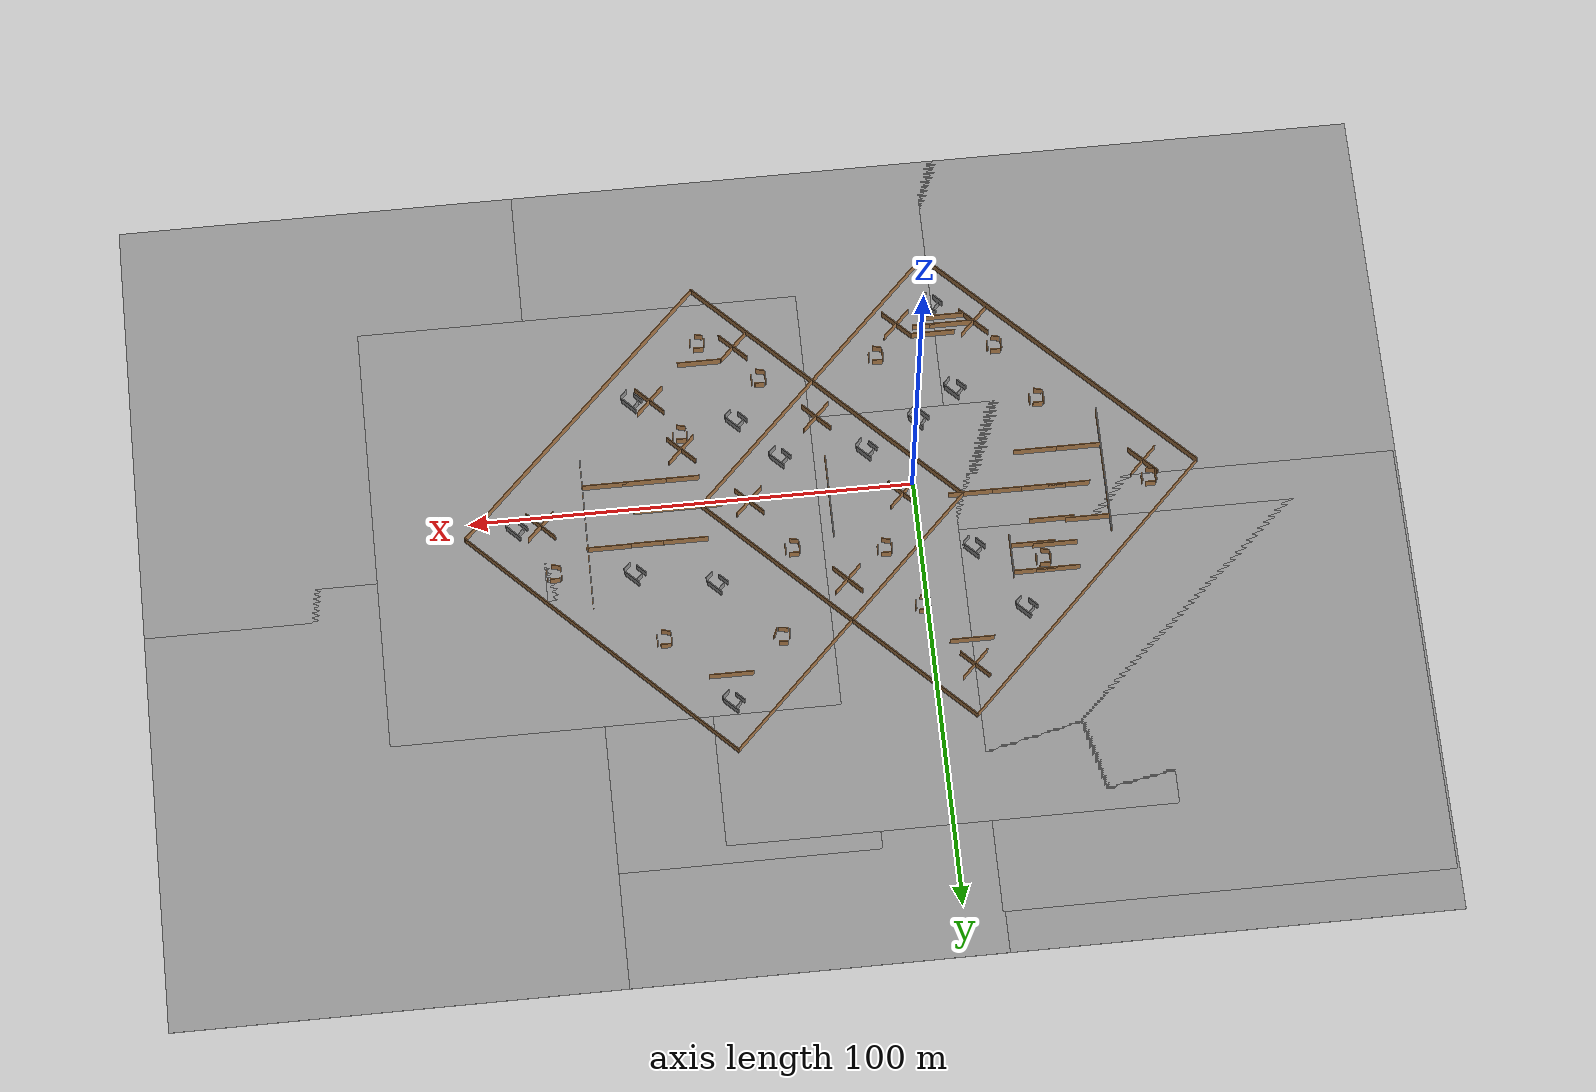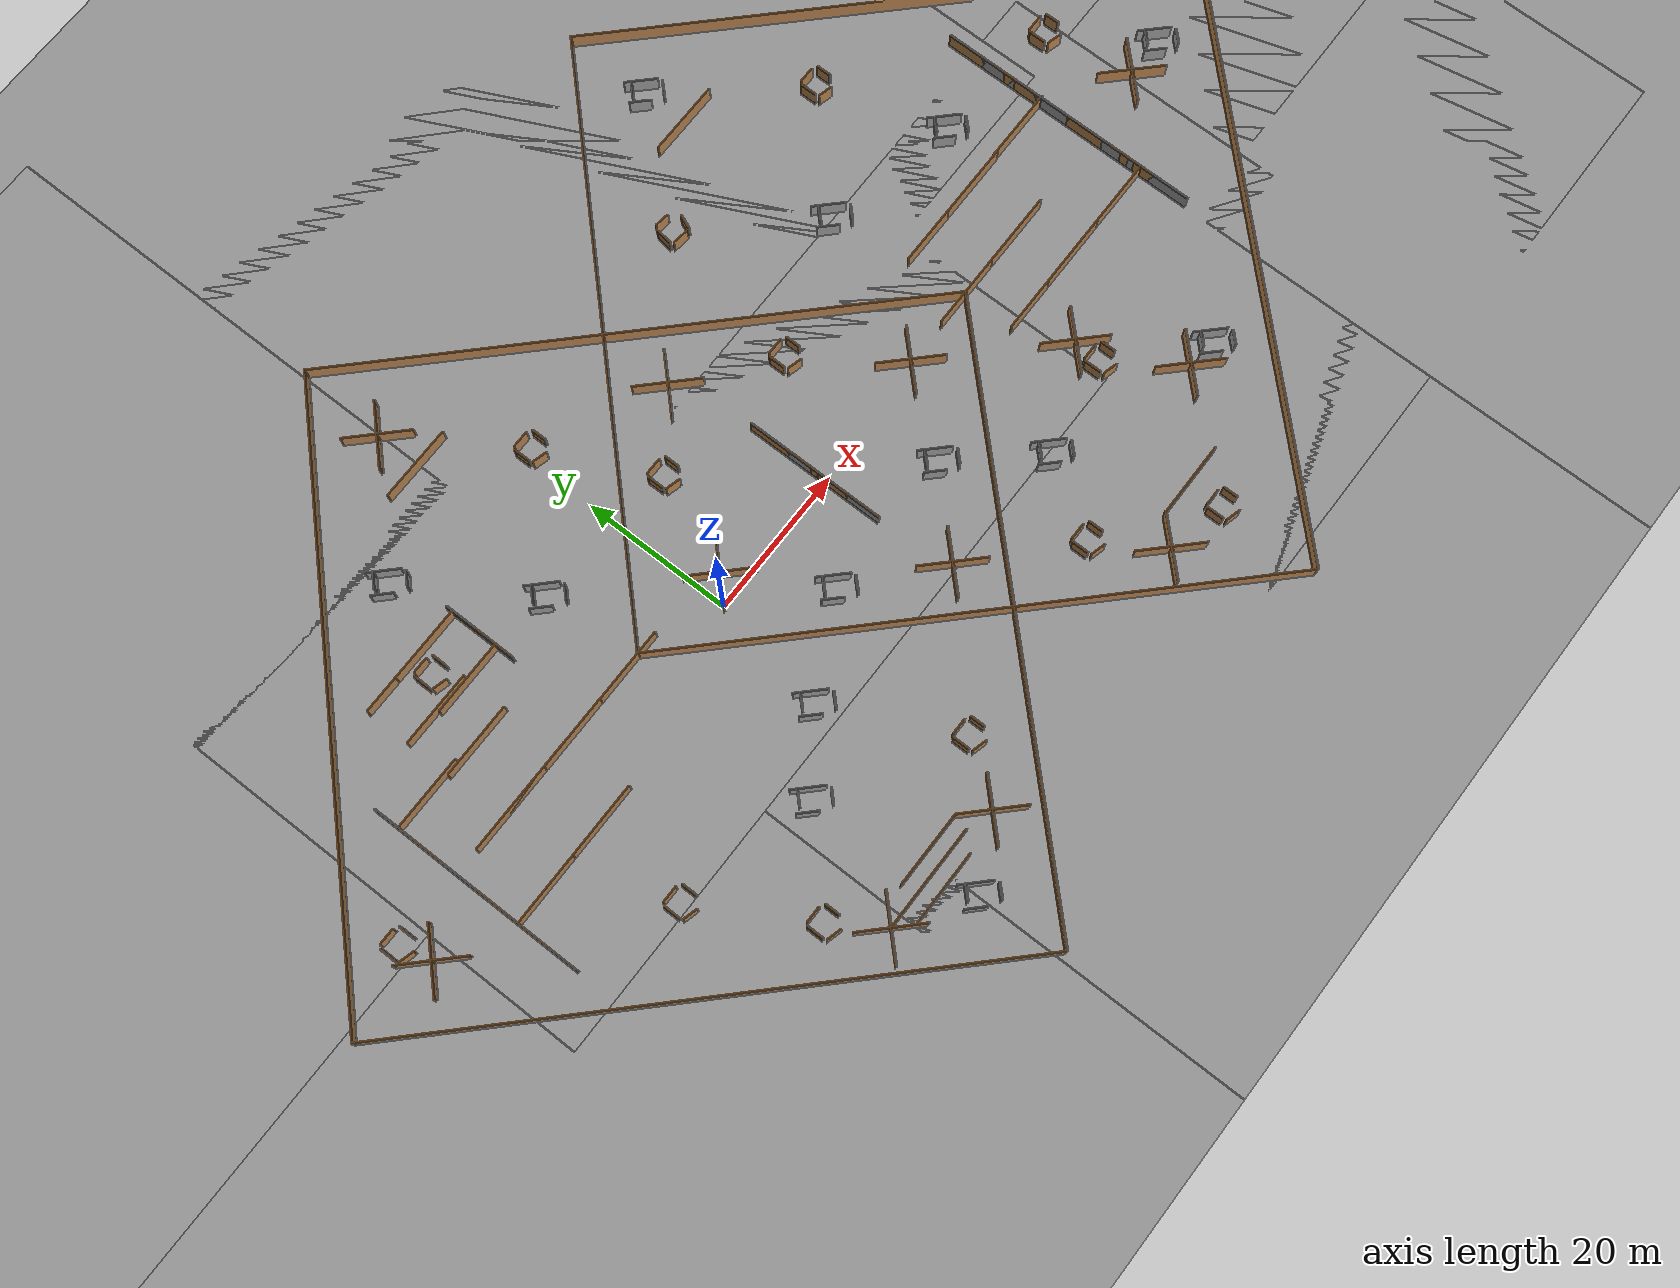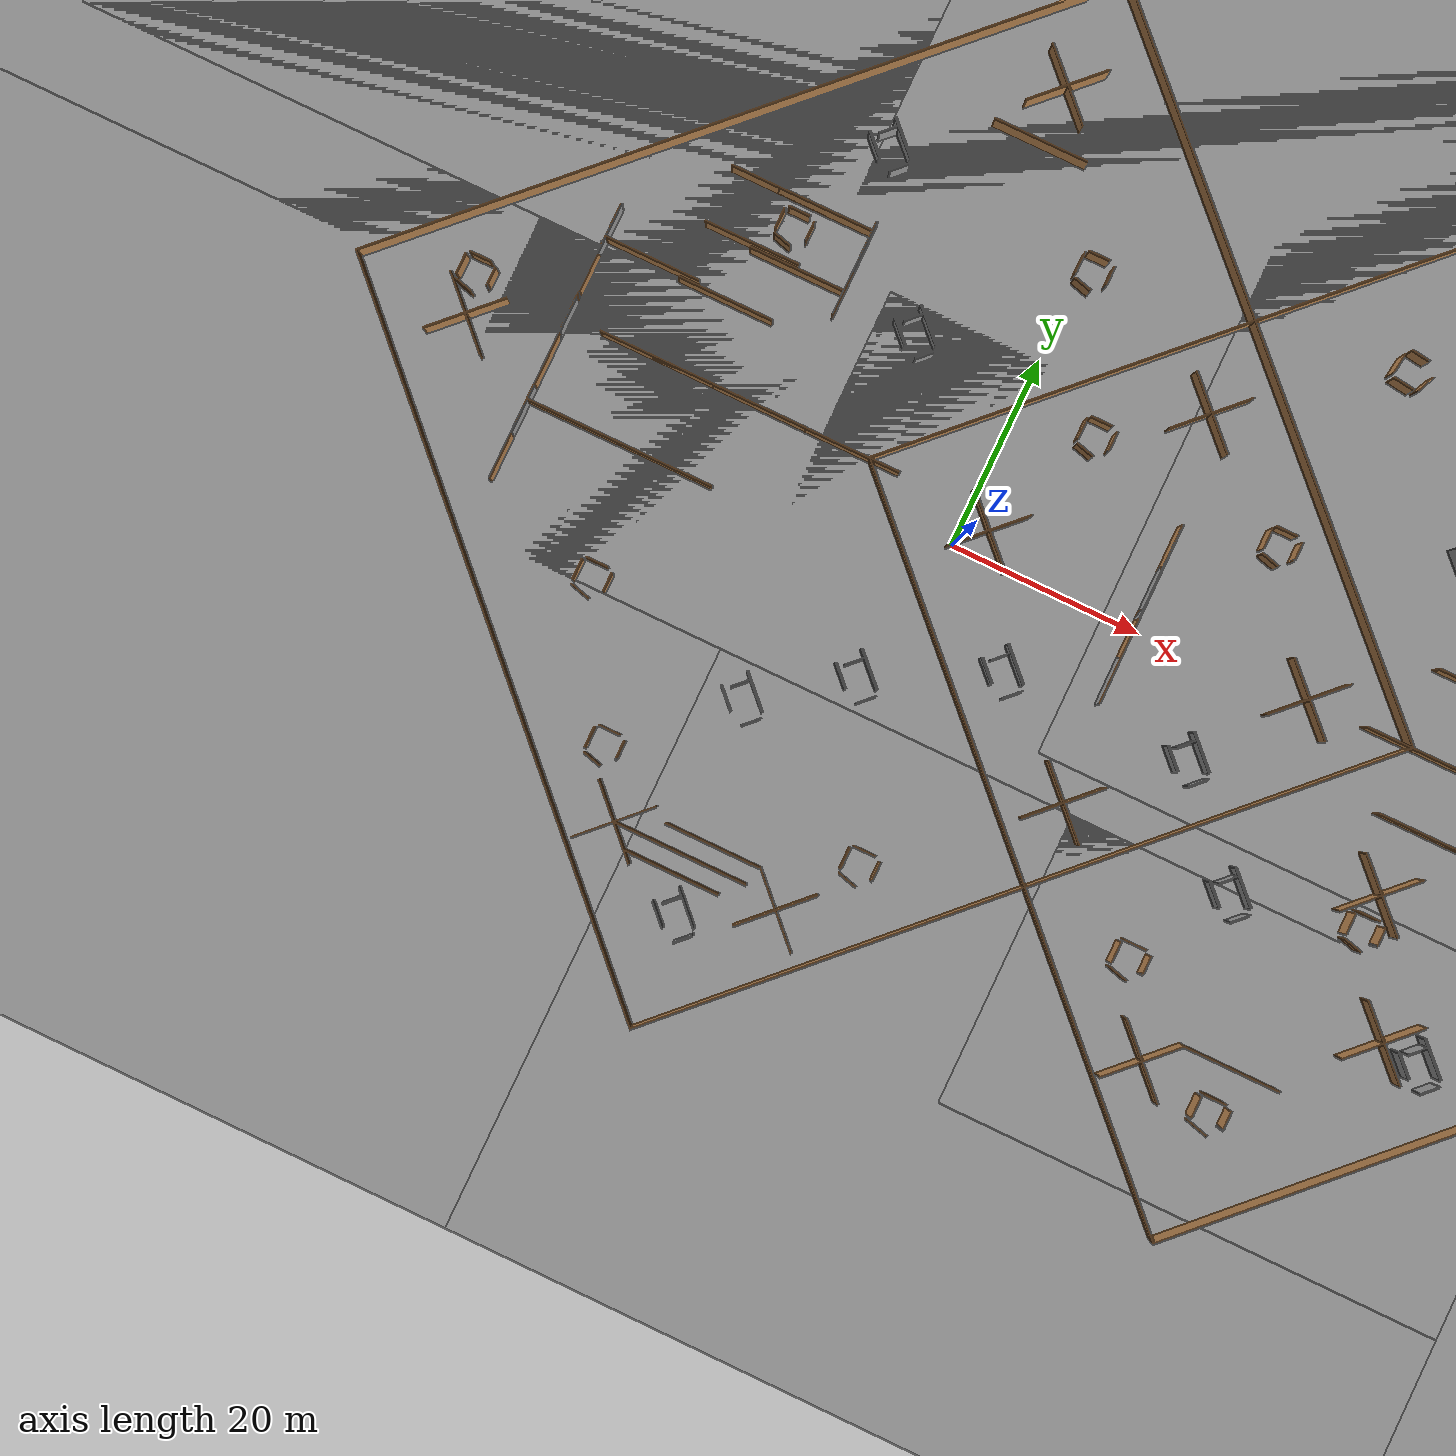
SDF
<sdf version="1.5">
 <world name="default">
  <model name="mard"><static>false</static></model>
  <light name="sun" type="directional">
   <pose>0 0 10 0 -0 0</pose>
   <diffuse>0.8 0.8 0.8 1</diffuse>
   <specular>0.2 0.2 0.2 1</specular>
   <attenuation>
    <range>1000</range>
    <constant>0.9</constant>
    <linear>0.01</linear>
    <quadratic>0.001</quadratic>
   </attenuation>
   <direction>-0.5 0.1 -0.9</direction>
  </light>
  <model name="ground_plane">
   <static>1</static>
   <link name="link">
    <collision name="collision">
     <geometry><plane><normal>0 0 1</normal><size>100 100</size></plane></geometry>
     <surface><friction><ode><mu>100</mu><mu2>50</mu2></ode></friction></surface>
    </collision>
    <visual name="visual">
     <cast_shadows>0</cast_shadows>
     <geometry><plane><normal>0 0 1</normal><size>100 100</size></plane></geometry>
     <material>
      <script><uri>file://media/materials/scripts/gazebo.material</uri><name>Gazebo/Grey</name></script>
     </material>
    </visual>
   </link>
  </model>
  <physics name="default_physics" default="0" type="ode">
   <max_step_size>0.001</max_step_size>
   <real_time_factor>1</real_time_factor>
   <real_time_update_rate>1000</real_time_update_rate>
   <gravity>0 0 -9.8</gravity>
   <magnetic_field>5.5645e-06 2.28758e-05 -4.23884e-05</magnetic_field>
  </physics>
  <scene><ambient>0.4 0.4 0.4 1</ambient><background>0.7 0.7 0.7 1</background><shadows>1</shadows></scene>
  <spherical_coordinates>
   <surface_model>EARTH_WGS84</surface_model>
   <latitude_deg>0</latitude_deg>
   <longitude_deg>0</longitude_deg>
   <elevation>0</elevation>
   <heading_deg>0</heading_deg>
  </spherical_coordinates>
  <model name="LoZ">
   <pose>-8.13692 1.02346 0 0 -0 0</pose>
   <link name="Wall_0">
    <collision name="Wall_0_Collision">
     <geometry><box><size>79.346 0.15 2.5</size></box></geometry>
     <pose>0 0 1.25 0 -0 0</pose>
    </collision>
    <visual name="Wall_0_Visual">
     <pose>0 0 1.25 0 -0 0</pose>
     <geometry><box><size>79.346 0.15 2.5</size></box></geometry>
     <material>
      <script><uri>file://media/materials/scripts/gazebo.material</uri><name>Gazebo/Wood</name></script>
      <ambient>1 1 1 1</ambient>
     </material>
    </visual>
    <pose>-28 -28 0 0 0 -0.785398</pose>
   </link>
   <link name="Wall_4">
    <collision name="Wall_4_Collision">
     <geometry><box><size>79.346 0.15 2.5</size></box></geometry>
     <pose>0 0 1.25 0 -0 0</pose>
    </collision>
    <visual name="Wall_4_Visual">
     <pose>0 0 1.25 0 -0 0</pose>
     <geometry><box><size>79.346 0.15 2.5</size></box></geometry>
     <material>
      <script><uri>file://media/materials/scripts/gazebo.material</uri><name>Gazebo/Wood</name></script>
      <ambient>1 1 1 1</ambient>
     </material>
    </visual>
    <pose>-28 28 0 0 -0 0.785398</pose>
   </link>
   <link name="Wall_6">
    <collision name="Wall_6_Collision">
     <geometry><box><size>79.346 0.15 2.5</size></box></geometry>
     <pose>0 0 1.25 0 -0 0</pose>
    </collision>
    <visual name="Wall_6_Visual">
     <pose>0 0 1.25 0 -0 0</pose>
     <geometry><box><size>79.346 0.15 2.5</size></box></geometry>
     <material>
      <script><uri>file://media/materials/scripts/gazebo.material</uri><name>Gazebo/Wood</name></script>
      <ambient>1 1 1 1</ambient>
     </material>
    </visual>
    <pose>28 28 0 0 -0 2.35619</pose>
   </link>
   <link name="Wall_8">
    <collision name="Wall_8_Collision">
     <geometry><box><size>79.346 0.15 2.5</size></box></geometry>
     <pose>0 0 1.25 0 -0 0</pose>
    </collision>
    <visual name="Wall_8_Visual">
     <pose>0 0 1.25 0 -0 0</pose>
     <geometry><box><size>79.346 0.15 2.5</size></box></geometry>
     <material>
      <script><uri>file://media/materials/scripts/gazebo.material</uri><name>Gazebo/Wood</name></script>
      <ambient>1 1 1 1</ambient>
     </material>
    </visual>
    <pose>28 -28 0 0 -0 0.785398</pose>
   </link>
   <static>1</static>
  </model>
  <model name="LoZ_0">
   <pose>45.13 4.02861 0 0 -0 0</pose>
   <link name="Wall_0">
    <collision name="Wall_0_Collision">
     <geometry><box><size>79.346 0.15 2.5</size></box></geometry>
     <pose>0 0 1.25 0 -0 0</pose>
    </collision>
    <visual name="Wall_0_Visual">
     <pose>0 0 1.25 0 -0 0</pose>
     <geometry><box><size>79.346 0.15 2.5</size></box></geometry>
     <material>
      <script><uri>file://media/materials/scripts/gazebo.material</uri><name>Gazebo/Wood</name></script>
      <ambient>1 1 1 1</ambient>
     </material>
    </visual>
    <pose>-28 -28 0 0 0 -0.785398</pose>
   </link>
   <link name="Wall_4">
    <collision name="Wall_4_Collision">
     <geometry><box><size>79.346 0.15 2.5</size></box></geometry>
     <pose>0 0 1.25 0 -0 0</pose>
    </collision>
    <visual name="Wall_4_Visual">
     <pose>0 0 1.25 0 -0 0</pose>
     <geometry><box><size>79.346 0.15 2.5</size></box></geometry>
     <material>
      <script><uri>file://media/materials/scripts/gazebo.material</uri><name>Gazebo/Wood</name></script>
      <ambient>1 1 1 1</ambient>
     </material>
    </visual>
    <pose>-28 28 0 0 -0 0.785398</pose>
   </link>
   <link name="Wall_6">
    <collision name="Wall_6_Collision">
     <geometry><box><size>79.346 0.15 2.5</size></box></geometry>
     <pose>0 0 1.25 0 -0 0</pose>
    </collision>
    <visual name="Wall_6_Visual">
     <pose>0 0 1.25 0 -0 0</pose>
     <geometry><box><size>79.346 0.15 2.5</size></box></geometry>
     <material>
      <script><uri>file://media/materials/scripts/gazebo.material</uri><name>Gazebo/Wood</name></script>
      <ambient>1 1 1 1</ambient>
     </material>
    </visual>
    <pose>28 28 0 0 -0 2.35619</pose>
   </link>
   <link name="Wall_8">
    <collision name="Wall_8_Collision">
     <geometry><box><size>79.346 0.15 2.5</size></box></geometry>
     <pose>0 0 1.25 0 -0 0</pose>
    </collision>
    <visual name="Wall_8_Visual">
     <pose>0 0 1.25 0 -0 0</pose>
     <geometry><box><size>79.346 0.15 2.5</size></box></geometry>
     <material>
      <script><uri>file://media/materials/scripts/gazebo.material</uri><name>Gazebo/Wood</name></script>
      <ambient>1 1 1 1</ambient>
     </material>
    </visual>
    <pose>28 -28 0 0 -0 0.785398</pose>
   </link>
   <static>1</static>
  </model>
  <model name="ground_plane_0">
   <static>1</static>
   <link name="link">
    <collision name="collision">
     <geometry><plane><normal>0 0 1</normal><size>100 100</size></plane></geometry>
     <surface><friction><ode><mu>100</mu><mu2>50</mu2></ode></friction></surface>
    </collision>
    <visual name="visual">
     <cast_shadows>0</cast_shadows>
     <geometry><plane><normal>0 0 1</normal><size>100 100</size></plane></geometry>
     <material>
      <script><uri>file://media/materials/scripts/gazebo.material</uri><name>Gazebo/Grey</name></script>
     </material>
    </visual>
   </link>
   <pose>0 31.4073 0 0 -0 0</pose>
  </model>
  <model name="ground_plane_1">
   <static>1</static>
   <link name="link">
    <collision name="collision">
     <geometry><plane><normal>0 0 1</normal><size>100 100</size></plane></geometry>
     <surface><friction><ode><mu>100</mu><mu2>50</mu2></ode></friction></surface>
    </collision>
    <visual name="visual">
     <cast_shadows>0</cast_shadows>
     <geometry><plane><normal>0 0 1</normal><size>100 100</size></plane></geometry>
     <material>
      <script><uri>file://media/materials/scripts/gazebo.material</uri><name>Gazebo/Grey</name></script>
     </material>
    </visual>
   </link>
   <pose>66 35.4819 0 0 -0 0</pose>
  </model>
  <model name="ground_plane_2">
   <static>1</static>
   <link name="link">
    <collision name="collision">
     <geometry><plane><normal>0 0 1</normal><size>100 100</size></plane></geometry>
     <surface><friction><ode><mu>100</mu><mu2>50</mu2></ode></friction></surface>
    </collision>
    <visual name="visual">
     <cast_shadows>0</cast_shadows>
     <geometry><plane><normal>0 0 1</normal><size>100 100</size></plane></geometry>
     <material>
      <script><uri>file://media/materials/scripts/gazebo.material</uri><name>Gazebo/Grey</name></script>
     </material>
    </visual>
   </link>
   <pose>71.5204 1 0 0 -0 0</pose>
  </model>
  <model name="ground_plane_3">
   <static>1</static>
   <link name="link">
    <collision name="collision">
     <geometry><plane><normal>0 0 1</normal><size>100 100</size></plane></geometry>
     <surface><friction><ode><mu>100</mu><mu2>50</mu2></ode></friction></surface>
    </collision>
    <visual name="visual">
     <cast_shadows>0</cast_shadows>
     <geometry><plane><normal>0 0 1</normal><size>100 100</size></plane></geometry>
     <material>
      <script><uri>file://media/materials/scripts/gazebo.material</uri><name>Gazebo/Grey</name></script>
     </material>
    </visual>
   </link>
   <pose>124 62 0 0 -0 0</pose>
  </model>
  <model name="ground_plane_4">
   <static>1</static>
   <link name="link">
    <collision name="collision">
     <geometry><plane><normal>0 0 1</normal><size>100 100</size></plane></geometry>
     <surface><friction><ode><mu>100</mu><mu2>50</mu2></ode></friction></surface>
    </collision>
    <visual name="visual">
     <cast_shadows>0</cast_shadows>
     <geometry><plane><normal>0 0 1</normal><size>100 100</size></plane></geometry>
     <material>
      <script><uri>file://media/materials/scripts/gazebo.material</uri><name>Gazebo/Grey</name></script>
     </material>
    </visual>
   </link>
   <pose>124 -30 0 0 -0 0</pose>
  </model>
  <model name="ground_plane_5">
   <static>1</static>
   <link name="link">
    <collision name="collision">
     <geometry><plane><normal>0 0 1</normal><size>100 100</size></plane></geometry>
     <surface><friction><ode><mu>100</mu><mu2>50</mu2></ode></friction></surface>
    </collision>
    <visual name="visual">
     <cast_shadows>0</cast_shadows>
     <geometry><plane><normal>0 0 1</normal><size>100 100</size></plane></geometry>
     <material>
      <script><uri>file://media/materials/scripts/gazebo.material</uri><name>Gazebo/Grey</name></script>
     </material>
    </visual>
   </link>
   <pose>34 -30 0 0 -0 0</pose>
  </model>
  <model name="ground_plane_6">
   <static>1</static>
   <link name="link">
    <collision name="collision">
     <geometry><plane><normal>0 0 1</normal><size>100 100</size></plane></geometry>
     <surface><friction><ode><mu>100</mu><mu2>50</mu2></ode></friction></surface>
    </collision>
    <visual name="visual">
     <cast_shadows>0</cast_shadows>
     <geometry><plane><normal>0 0 1</normal><size>100 100</size></plane></geometry>
     <material>
      <script><uri>file://media/materials/scripts/gazebo.material</uri><name>Gazebo/Grey</name></script>
     </material>
    </visual>
   </link>
   <pose>-59 -30 0 0 -0 0</pose>
  </model>
  <model name="ground_plane_7">
   <static>1</static>
   <link name="link">
    <collision name="collision">
     <geometry><plane><normal>0 0 1</normal><size>100 100</size></plane></geometry>
     <surface><friction><ode><mu>100</mu><mu2>50</mu2></ode></friction></surface>
    </collision>
    <visual name="visual">
     <cast_shadows>0</cast_shadows>
     <geometry><plane><normal>0 0 1</normal><size>100 100</size></plane></geometry>
     <material>
      <script><uri>file://media/materials/scripts/gazebo.material</uri><name>Gazebo/Grey</name></script>
     </material>
    </visual>
   </link>
   <pose>-58.5079 52.5615 0 0 -0 0</pose>
  </model>
  <model name="ground_plane_8">
   <static>1</static>
   <link name="link">
    <collision name="collision">
     <geometry><plane><normal>0 0 1</normal><size>100 100</size></plane></geometry>
     <surface><friction><ode><mu>100</mu><mu2>50</mu2></ode></friction></surface>
    </collision>
    <visual name="visual">
     <cast_shadows>0</cast_shadows>
     <geometry><plane><normal>0 0 1</normal><size>100 100</size></plane></geometry>
     <material>
      <script><uri>file://media/materials/scripts/gazebo.material</uri><name>Gazebo/Grey</name></script>
     </material>
    </visual>
   </link>
   <pose>27 62 0 0 -0 0</pose>
  </model>
  <model name="ground_plane_9">
   <static>1</static>
   <link name="link">
    <collision name="collision">
     <geometry><plane><normal>0 0 1</normal><size>100 100</size></plane></geometry>
     <surface><friction><ode><mu>100</mu><mu2>50</mu2></ode></friction></surface>
    </collision>
    <visual name="visual">
     <cast_shadows>0</cast_shadows>
     <geometry><plane><normal>0 0 1</normal><size>100 100</size></plane></geometry>
     <material>
      <script><uri>file://media/materials/scripts/gazebo.material</uri><name>Gazebo/Grey</name></script>
     </material>
    </visual>
   </link>
   <pose>-59 62 0 0 -0 0</pose>
  </model>
  <model name="wall-10m-amodi_0">
   <pose>-43 11 0 0 -0 0</pose>
   <link name="Wall_24">
    <collision name="Wall_24_Collision">
     <geometry><box><size>10 0.15 2.5</size></box></geometry>
     <pose>0 0 1.25 0 -0 0</pose>
    </collision>
    <visual name="Wall_24_Visual">
     <pose>0 0 1.25 0 -0 0</pose>
     <geometry><box><size>10 0.15 2.5</size></box></geometry>
     <material>
      <script><uri>file://media/materials/scripts/gazebo.material</uri><name>Gazebo/Grey</name></script>
      <ambient>1 1 1 1</ambient>
     </material>
    </visual>
    <pose>0 -0 0 0 0 -1.5708</pose>
   </link>
   <link name="Wall_25">
    <collision name="Wall_25_Collision">
     <geometry><box><size>10 0.15 2.5</size></box></geometry>
     <pose>0 0 1.25 0 -0 0</pose>
    </collision>
    <visual name="Wall_25_Visual">
     <pose>0 0 1.25 0 -0 0</pose>
     <geometry><box><size>10 0.15 2.5</size></box></geometry>
     <material>
      <script><uri>file://media/materials/scripts/gazebo.material</uri><name>Gazebo/Wood</name></script>
      <ambient>1 1 1 1</ambient>
     </material>
    </visual>
    <pose>0 -0 0 0 -0 1.5708</pose>
   </link>
   <static>1</static>
  </model>
  <model name="wall-10m-amodi_1">
   <pose>-43 1.54678 0 0 -0 0</pose>
   <link name="Wall_24">
    <collision name="Wall_24_Collision">
     <geometry><box><size>10 0.15 2.5</size></box></geometry>
     <pose>0 0 1.25 0 -0 0</pose>
    </collision>
    <visual name="Wall_24_Visual">
     <pose>0 0 1.25 0 -0 0</pose>
     <geometry><box><size>10 0.15 2.5</size></box></geometry>
     <material>
      <script><uri>file://media/materials/scripts/gazebo.material</uri><name>Gazebo/Grey</name></script>
      <ambient>1 1 1 1</ambient>
     </material>
    </visual>
    <pose>0 -0 0 0 0 -1.5708</pose>
   </link>
   <link name="Wall_25">
    <collision name="Wall_25_Collision">
     <geometry><box><size>10 0.15 2.5</size></box></geometry>
     <pose>0 0 1.25 0 -0 0</pose>
    </collision>
    <visual name="Wall_25_Visual">
     <pose>0 0 1.25 0 -0 0</pose>
     <geometry><box><size>10 0.15 2.5</size></box></geometry>
     <material>
      <script><uri>file://media/materials/scripts/gazebo.material</uri><name>Gazebo/Wood</name></script>
      <ambient>1 1 1 1</ambient>
     </material>
    </visual>
    <pose>0 -0 0 0 -0 1.5708</pose>
   </link>
   <static>1</static>
  </model>
  <model name="wall-10m-amodi_2">
   <pose>-43 -8.4725 0 0 -0 0</pose>
   <link name="Wall_24">
    <collision name="Wall_24_Collision">
     <geometry><box><size>10 0.15 2.5</size></box></geometry>
     <pose>0 0 1.25 0 -0 0</pose>
    </collision>
    <visual name="Wall_24_Visual">
     <pose>0 0 1.25 0 -0 0</pose>
     <geometry><box><size>10 0.15 2.5</size></box></geometry>
     <material>
      <script><uri>file://media/materials/scripts/gazebo.material</uri><name>Gazebo/Grey</name></script>
      <ambient>1 1 1 1</ambient>
     </material>
    </visual>
    <pose>0 -0 0 0 0 -1.5708</pose>
   </link>
   <link name="Wall_25">
    <collision name="Wall_25_Collision">
     <geometry><box><size>10 0.15 2.5</size></box></geometry>
     <pose>0 0 1.25 0 -0 0</pose>
    </collision>
    <visual name="Wall_25_Visual">
     <pose>0 0 1.25 0 -0 0</pose>
     <geometry><box><size>10 0.15 2.5</size></box></geometry>
     <material>
      <script><uri>file://media/materials/scripts/gazebo.material</uri><name>Gazebo/Wood</name></script>
      <ambient>1 1 1 1</ambient>
     </material>
    </visual>
    <pose>0 -0 0 0 -0 1.5708</pose>
   </link>
   <static>1</static>
  </model>
  <model name="wall-10m-ofoghi">
   <pose>-37.9745 -4.98114 0 0 -0 0</pose>
   <link name="Wall_22">
    <collision name="Wall_22_Collision">
     <geometry><box><size>10 0.15 2.5</size></box></geometry>
     <pose>0 0 1.25 0 -0 0</pose>
    </collision>
    <visual name="Wall_22_Visual">
     <pose>0 0 1.25 0 -0 0</pose>
     <geometry><box><size>10 0.15 2.5</size></box></geometry>
     <material>
      <script><uri>file://media/materials/scripts/gazebo.material</uri><name>Gazebo/Wood</name></script>
      <ambient>1 1 1 1</ambient>
     </material>
    </visual>
   </link>
   <static>1</static>
  </model>
  <model name="wall-10m-ofoghi_0">
   <pose>-28.366 -4.98164 0 0 -0 0</pose>
   <link name="Wall_22">
    <collision name="Wall_22_Collision">
     <geometry><box><size>10 0.15 2.5</size></box></geometry>
     <pose>0 0 1.25 0 -0 0</pose>
    </collision>
    <visual name="Wall_22_Visual">
     <pose>0 0 1.25 0 -0 0</pose>
     <geometry><box><size>10 0.15 2.5</size></box></geometry>
     <material>
      <script><uri>file://media/materials/scripts/gazebo.material</uri><name>Gazebo/Wood</name></script>
      <ambient>1 1 1 1</ambient>
     </material>
    </visual>
   </link>
   <static>1</static>
  </model>
  <model name="wall-10m-amodi_3">
   <pose>74 18 0 0 -0 0</pose>
   <link name="Wall_24">
    <collision name="Wall_24_Collision">
     <geometry><box><size>10 0.15 2.5</size></box></geometry>
     <pose>0 0 1.25 0 -0 0</pose>
    </collision>
    <visual name="Wall_24_Visual">
     <pose>0 0 1.25 0 -0 0</pose>
     <geometry><box><size>10 0.15 2.5</size></box></geometry>
     <material>
      <script><uri>file://media/materials/scripts/gazebo.material</uri><name>Gazebo/Grey</name></script>
      <ambient>1 1 1 1</ambient>
     </material>
    </visual>
    <pose>0 -0 0 0 0 -1.5708</pose>
   </link>
   <link name="Wall_25">
    <collision name="Wall_25_Collision">
     <geometry><box><size>10 0.15 2.5</size></box></geometry>
     <pose>0 0 1.25 0 -0 0</pose>
    </collision>
    <visual name="Wall_25_Visual">
     <pose>0 0 1.25 0 -0 0</pose>
     <geometry><box><size>10 0.15 2.5</size></box></geometry>
     <material>
      <script><uri>file://media/materials/scripts/gazebo.material</uri><name>Gazebo/Wood</name></script>
      <ambient>1 1 1 1</ambient>
     </material>
    </visual>
    <pose>0 -0 0 0 -0 1.5708</pose>
   </link>
   <static>1</static>
  </model>
  <model name="wall-10m-amodi_4">
   <pose>74 9.59679 0 0 -0 0</pose>
   <link name="Wall_24">
    <collision name="Wall_24_Collision">
     <geometry><box><size>10 0.15 2.5</size></box></geometry>
     <pose>0 0 1.25 0 -0 0</pose>
    </collision>
    <visual name="Wall_24_Visual">
     <pose>0 0 1.25 0 -0 0</pose>
     <geometry><box><size>10 0.15 2.5</size></box></geometry>
     <material>
      <script><uri>file://media/materials/scripts/gazebo.material</uri><name>Gazebo/Grey</name></script>
      <ambient>1 1 1 1</ambient>
     </material>
    </visual>
    <pose>0 -0 0 0 0 -1.5708</pose>
   </link>
   <link name="Wall_25">
    <collision name="Wall_25_Collision">
     <geometry><box><size>10 0.15 2.5</size></box></geometry>
     <pose>0 0 1.25 0 -0 0</pose>
    </collision>
    <visual name="Wall_25_Visual">
     <pose>0 0 1.25 0 -0 0</pose>
     <geometry><box><size>10 0.15 2.5</size></box></geometry>
     <material>
      <script><uri>file://media/materials/scripts/gazebo.material</uri><name>Gazebo/Wood</name></script>
      <ambient>1 1 1 1</ambient>
     </material>
    </visual>
    <pose>0 -0 0 0 -0 1.5708</pose>
   </link>
   <static>1</static>
  </model>
  <model name="wall-10m-amodi_5">
   <pose>74 0 0 0 -0 0</pose>
   <link name="Wall_24">
    <collision name="Wall_24_Collision">
     <geometry><box><size>10 0.15 2.5</size></box></geometry>
     <pose>0 0 1.25 0 -0 0</pose>
    </collision>
    <visual name="Wall_24_Visual">
     <pose>0 0 1.25 0 -0 0</pose>
     <geometry><box><size>10 0.15 2.5</size></box></geometry>
     <material>
      <script><uri>file://media/materials/scripts/gazebo.material</uri><name>Gazebo/Grey</name></script>
      <ambient>1 1 1 1</ambient>
     </material>
    </visual>
    <pose>0 -0 0 0 0 -1.5708</pose>
   </link>
   <link name="Wall_25">
    <collision name="Wall_25_Collision">
     <geometry><box><size>10 0.15 2.5</size></box></geometry>
     <pose>0 0 1.25 0 -0 0</pose>
    </collision>
    <visual name="Wall_25_Visual">
     <pose>0 0 1.25 0 -0 0</pose>
     <geometry><box><size>10 0.15 2.5</size></box></geometry>
     <material>
      <script><uri>file://media/materials/scripts/gazebo.material</uri><name>Gazebo/Wood</name></script>
      <ambient>1 1 1 1</ambient>
     </material>
    </visual>
    <pose>0 -0 0 0 -0 1.5708</pose>
   </link>
   <static>1</static>
  </model>
  <model name="wall-10m-amodi_6">
   <pose>74 -8 0 0 -0 0</pose>
   <link name="Wall_24">
    <collision name="Wall_24_Collision">
     <geometry><box><size>10 0.15 2.5</size></box></geometry>
     <pose>0 0 1.25 0 -0 0</pose>
    </collision>
    <visual name="Wall_24_Visual">
     <pose>0 0 1.25 0 -0 0</pose>
     <geometry><box><size>10 0.15 2.5</size></box></geometry>
     <material>
      <script><uri>file://media/materials/scripts/gazebo.material</uri><name>Gazebo/Grey</name></script>
      <ambient>1 1 1 1</ambient>
     </material>
    </visual>
    <pose>0 -0 0 0 0 -1.5708</pose>
   </link>
   <link name="Wall_25">
    <collision name="Wall_25_Collision">
     <geometry><box><size>10 0.15 2.5</size></box></geometry>
     <pose>0 0 1.25 0 -0 0</pose>
    </collision>
    <visual name="Wall_25_Visual">
     <pose>0 0 1.25 0 -0 0</pose>
     <geometry><box><size>10 0.15 2.5</size></box></geometry>
     <material>
      <script><uri>file://media/materials/scripts/gazebo.material</uri><name>Gazebo/Wood</name></script>
      <ambient>1 1 1 1</ambient>
     </material>
    </visual>
    <pose>0 -0 0 0 -0 1.5708</pose>
   </link>
   <static>1</static>
  </model>
  <model name="wall-10m-ofoghi_1">
   <pose>59.8981 8.99105 0 0 -0 0</pose>
   <link name="Wall_22">
    <collision name="Wall_22_Collision">
     <geometry><box><size>10 0.15 2.5</size></box></geometry>
     <pose>0 0 1.25 0 -0 0</pose>
    </collision>
    <visual name="Wall_22_Visual">
     <pose>0 0 1.25 0 -0 0</pose>
     <geometry><box><size>10 0.15 2.5</size></box></geometry>
     <material>
      <script><uri>file://media/materials/scripts/gazebo.material</uri><name>Gazebo/Wood</name></script>
      <ambient>1 1 1 1</ambient>
     </material>
    </visual>
   </link>
   <static>1</static>
  </model>
  <model name="wall-10m-ofoghi_2">
   <pose>69.2605 9.07388 0 0 -0 0</pose>
   <link name="Wall_22">
    <collision name="Wall_22_Collision">
     <geometry><box><size>10 0.15 2.5</size></box></geometry>
     <pose>0 0 1.25 0 -0 0</pose>
    </collision>
    <visual name="Wall_22_Visual">
     <pose>0 0 1.25 0 -0 0</pose>
     <geometry><box><size>10 0.15 2.5</size></box></geometry>
     <material>
      <script><uri>file://media/materials/scripts/gazebo.material</uri><name>Gazebo/Wood</name></script>
      <ambient>1 1 1 1</ambient>
     </material>
    </visual>
   </link>
   <static>1</static>
  </model>
  <model name="wall-10m-ofoghi_3">
   <pose>-38 12.4908 0 0 -0 0</pose>
   <link name="Wall_22">
    <collision name="Wall_22_Collision">
     <geometry><box><size>10 0.15 2.5</size></box></geometry>
     <pose>0 0 1.25 0 -0 0</pose>
    </collision>
    <visual name="Wall_22_Visual">
     <pose>0 0 1.25 0 -0 0</pose>
     <geometry><box><size>10 0.15 2.5</size></box></geometry>
     <material>
      <script><uri>file://media/materials/scripts/gazebo.material</uri><name>Gazebo/Wood</name></script>
      <ambient>1 1 1 1</ambient>
     </material>
    </visual>
   </link>
   <static>1</static>
  </model>
  <model name="wall-10m-ofoghi_4">
   <pose>-30 12 0 0 -0 0</pose>
   <link name="Wall_22">
    <collision name="Wall_22_Collision">
     <geometry><box><size>10 0.15 2.5</size></box></geometry>
     <pose>0 0 1.25 0 -0 0</pose>
    </collision>
    <visual name="Wall_22_Visual">
     <pose>0 0 1.25 0 -0 0</pose>
     <geometry><box><size>10 0.15 2.5</size></box></geometry>
     <material>
      <script><uri>file://media/materials/scripts/gazebo.material</uri><name>Gazebo/Wood</name></script>
      <ambient>1 1 1 1</ambient>
     </material>
    </visual>
   </link>
   <static>1</static>
  </model>
  <model name="wall-10m-ofoghi_5">
   <pose>-12.6357 3.95502 0 0 -0 0</pose>
   <link name="Wall_22">
    <collision name="Wall_22_Collision">
     <geometry><box><size>10 0.15 2.5</size></box></geometry>
     <pose>0 0 1.25 0 -0 0</pose>
    </collision>
    <visual name="Wall_22_Visual">
     <pose>0 0 1.25 0 -0 0</pose>
     <geometry><box><size>10 0.15 2.5</size></box></geometry>
     <material>
      <script><uri>file://media/materials/scripts/gazebo.material</uri><name>Gazebo/Wood</name></script>
      <ambient>1 1 1 1</ambient>
     </material>
    </visual>
   </link>
   <static>1</static>
  </model>
  <model name="wall-10m-ofoghi_6">
   <pose>-22.5687 3.97573 0 0 -0 0</pose>
   <link name="Wall_22">
    <collision name="Wall_22_Collision">
     <geometry><box><size>10 0.15 2.5</size></box></geometry>
     <pose>0 0 1.25 0 -0 0</pose>
    </collision>
    <visual name="Wall_22_Visual">
     <pose>0 0 1.25 0 -0 0</pose>
     <geometry><box><size>10 0.15 2.5</size></box></geometry>
     <material>
      <script><uri>file://media/materials/scripts/gazebo.material</uri><name>Gazebo/Wood</name></script>
      <ambient>1 1 1 1</ambient>
     </material>
    </visual>
   </link>
   <static>1</static>
  </model>
  <model name="wall-10m-ofoghi_7">
   <pose>48 1 0 0 -0 0</pose>
   <link name="Wall_22">
    <collision name="Wall_22_Collision">
     <geometry><box><size>10 0.15 2.5</size></box></geometry>
     <pose>0 0 1.25 0 -0 0</pose>
    </collision>
    <visual name="Wall_22_Visual">
     <pose>0 0 1.25 0 -0 0</pose>
     <geometry><box><size>10 0.15 2.5</size></box></geometry>
     <material>
      <script><uri>file://media/materials/scripts/gazebo.material</uri><name>Gazebo/Wood</name></script>
      <ambient>1 1 1 1</ambient>
     </material>
    </visual>
   </link>
   <static>1</static>
  </model>
  <model name="wall-10m-ofoghi_8">
   <pose>58 1 0 0 -0 0</pose>
   <link name="Wall_22">
    <collision name="Wall_22_Collision">
     <geometry><box><size>10 0.15 2.5</size></box></geometry>
     <pose>0 0 1.25 0 -0 0</pose>
    </collision>
    <visual name="Wall_22_Visual">
     <pose>0 0 1.25 0 -0 0</pose>
     <geometry><box><size>10 0.15 2.5</size></box></geometry>
     <material>
      <script><uri>file://media/materials/scripts/gazebo.material</uri><name>Gazebo/Wood</name></script>
      <ambient>1 1 1 1</ambient>
     </material>
    </visual>
   </link>
   <static>1</static>
  </model>
  <model name="wall-10m-ofoghi_9">
   <pose>69 -6 0 0 -0 0</pose>
   <link name="Wall_22">
    <collision name="Wall_22_Collision">
     <geometry><box><size>10 0.15 2.5</size></box></geometry>
     <pose>0 0 1.25 0 -0 0</pose>
    </collision>
    <visual name="Wall_22_Visual">
     <pose>0 0 1.25 0 -0 0</pose>
     <geometry><box><size>10 0.15 2.5</size></box></geometry>
     <material>
      <script><uri>file://media/materials/scripts/gazebo.material</uri><name>Gazebo/Wood</name></script>
      <ambient>1 1 1 1</ambient>
     </material>
    </visual>
   </link>
   <static>1</static>
  </model>
  <model name="wall-10m-ofoghi_10">
   <pose>60 -6 0 0 -0 0</pose>
   <link name="Wall_22">
    <collision name="Wall_22_Collision">
     <geometry><box><size>10 0.15 2.5</size></box></geometry>
     <pose>0 0 1.25 0 -0 0</pose>
    </collision>
    <visual name="Wall_22_Visual">
     <pose>0 0 1.25 0 -0 0</pose>
     <geometry><box><size>10 0.15 2.5</size></box></geometry>
     <material>
      <script><uri>file://media/materials/scripts/gazebo.material</uri><name>Gazebo/Wood</name></script>
      <ambient>1 1 1 1</ambient>
     </material>
    </visual>
   </link>
   <static>1</static>
  </model>
  <model name="wall-10m-ofoghi_11">
   <pose>-9 -38 0 0 -0 0</pose>
   <link name="Wall_22">
    <collision name="Wall_22_Collision">
     <geometry><box><size>10 0.15 2.5</size></box></geometry>
     <pose>0 0 1.25 0 -0 0</pose>
    </collision>
    <visual name="Wall_22_Visual">
     <pose>0 0 1.25 0 -0 0</pose>
     <geometry><box><size>10 0.15 2.5</size></box></geometry>
     <material>
      <script><uri>file://media/materials/scripts/gazebo.material</uri><name>Gazebo/Wood</name></script>
      <ambient>1 1 1 1</ambient>
     </material>
    </visual>
   </link>
   <static>1</static>
  </model>
  <model name="wall-10m-ofoghi_12">
   <pose>-9 39 0 0 -0 0</pose>
   <link name="Wall_22">
    <collision name="Wall_22_Collision">
     <geometry><box><size>10 0.15 2.5</size></box></geometry>
     <pose>0 0 1.25 0 -0 0</pose>
    </collision>
    <visual name="Wall_22_Visual">
     <pose>0 0 1.25 0 -0 0</pose>
     <geometry><box><size>10 0.15 2.5</size></box></geometry>
     <material>
      <script><uri>file://media/materials/scripts/gazebo.material</uri><name>Gazebo/Wood</name></script>
      <ambient>1 1 1 1</ambient>
     </material>
    </visual>
   </link>
   <static>1</static>
  </model>
  <model name="wall-10m-ofoghi_13">
   <pose>45 -34 0 0 -0 0</pose>
   <link name="Wall_22">
    <collision name="Wall_22_Collision">
     <geometry><box><size>10 0.15 2.5</size></box></geometry>
     <pose>0 0 1.25 0 -0 0</pose>
    </collision>
    <visual name="Wall_22_Visual">
     <pose>0 0 1.25 0 -0 0</pose>
     <geometry><box><size>10 0.15 2.5</size></box></geometry>
     <material>
      <script><uri>file://media/materials/scripts/gazebo.material</uri><name>Gazebo/Wood</name></script>
      <ambient>1 1 1 1</ambient>
     </material>
    </visual>
   </link>
   <static>1</static>
  </model>
  <model name="wall-10m-ofoghi_14">
   <pose>45 42 0 0 -0 0</pose>
   <link name="Wall_22">
    <collision name="Wall_22_Collision">
     <geometry><box><size>10 0.15 2.5</size></box></geometry>
     <pose>0 0 1.25 0 -0 0</pose>
    </collision>
    <visual name="Wall_22_Visual">
     <pose>0 0 1.25 0 -0 0</pose>
     <geometry><box><size>10 0.15 2.5</size></box></geometry>
     <material>
      <script><uri>file://media/materials/scripts/gazebo.material</uri><name>Gazebo/Wood</name></script>
      <ambient>1 1 1 1</ambient>
     </material>
    </visual>
   </link>
   <static>1</static>
  </model>
  <model name="obs1">
   <pose>-52.8584 3.84332 0 0 -0 0</pose>
   <link name="Wall_10">
    <collision name="Wall_10_Collision">
     <geometry><box><size>2 0.15 2.5</size></box></geometry>
     <pose>0 0 1.25 0 -0 0</pose>
    </collision>
    <visual name="Wall_10_Visual">
     <pose>0 0 1.25 0 -0 0</pose>
     <geometry><box><size>2 0.15 2.5</size></box></geometry>
     <material>
      <script><uri>file://media/materials/scripts/gazebo.material</uri><name>Gazebo/Wood</name></script>
      <ambient>1 1 1 1</ambient>
     </material>
    </visual>
    <pose>-0.505188 -1.46687 0 0 0 -0.261799</pose>
   </link>
   <link name="Wall_2">
    <collision name="Wall_2_Collision">
     <geometry><box><size>2.25 0.15 2.5</size></box></geometry>
     <pose>0 0 1.25 0 -0 0</pose>
    </collision>
    <visual name="Wall_2_Visual">
     <pose>0 0 1.25 0 -0 0</pose>
     <geometry><box><size>2.25 0.15 2.5</size></box></geometry>
     <material>
      <script><uri>file://media/materials/scripts/gazebo.material</uri><name>Gazebo/Wood</name></script>
      <ambient>1 1 1 1</ambient>
     </material>
    </visual>
    <pose>-1.58039 0.313508 0 0 0 -1.5708</pose>
   </link>
   <link name="Wall_5">
    <collision name="Wall_5_Collision">
     <geometry><box><size>2.25 0.15 2.5</size></box></geometry>
     <pose>0 0 1.25 0 -0 0</pose>
    </collision>
    <visual name="Wall_5_Visual">
     <pose>0 0 1.25 0 -0 0</pose>
     <geometry><box><size>2.25 0.15 2.5</size></box></geometry>
     <material>
      <script><uri>file://media/materials/scripts/gazebo.material</uri><name>Gazebo/Wood</name></script>
      <ambient>1 1 1 1</ambient>
     </material>
    </visual>
    <pose>-0.185262 1.72313 0 0 -0 0</pose>
   </link>
   <link name="Wall_7">
    <collision name="Wall_7_Collision">
     <geometry><box><size>2 0.15 2.5</size></box></geometry>
     <pose>0 0 1.25 0 -0 0</pose>
    </collision>
    <visual name="Wall_7_Visual">
     <pose>0 0 1.25 0 -0 0</pose>
     <geometry><box><size>2 0.15 2.5</size></box></geometry>
     <material>
      <script><uri>file://media/materials/scripts/gazebo.material</uri><name>Gazebo/Wood</name></script>
      <ambient>1 1 1 1</ambient>
     </material>
    </visual>
    <pose>1.58039 0.398833 0 0 0 -1.5708</pose>
   </link>
   <link name="Wall_8">
    <collision name="Wall_8_Collision">
     <geometry><box><size>0.15 0.15 2.5</size></box></geometry>
     <pose>0 0 1.25 0 -0 0</pose>
    </collision>
    <visual name="Wall_8_Visual">
     <pose>0 0 1.25 0 -0 0</pose>
     <geometry><box><size>0.15 0.15 2.5</size></box></geometry>
     <material>
      <script><uri>file://media/materials/scripts/gazebo.material</uri><name>Gazebo/Grey</name></script>
      <ambient>1 1 1 1</ambient>
     </material>
    </visual>
    <pose>1.58039 -0.526167 0 0 -0 0</pose>
   </link>
   <static>1</static>
  </model>
  <model name="obs2">
   <pose>-9 -43.4324 0 0 -0 0</pose>
   <link name="Wall_0">
    <collision name="Wall_0_Collision">
     <geometry><box><size>2 0.15 2.5</size></box></geometry>
     <pose>0 0 1.25 0 -0 0</pose>
    </collision>
    <visual name="Wall_0_Visual">
     <pose>0 0 1.25 0 -0 0</pose>
     <geometry><box><size>2 0.15 2.5</size></box></geometry>
     <material>
      <script><uri>file://media/materials/scripts/gazebo.material</uri><name>Gazebo/Grey</name></script>
      <ambient>1 1 1 1</ambient>
     </material>
    </visual>
    <pose>-0.796332 1.10862 0 0 -0 0.785398</pose>
   </link>
   <link name="Wall_2">
    <collision name="Wall_2_Collision">
     <geometry><box><size>4.25 0.15 2.5</size></box></geometry>
     <pose>0 0 1.25 0 -0 0</pose>
    </collision>
    <visual name="Wall_2_Visual">
     <pose>0 0 1.25 0 -0 0</pose>
     <geometry><box><size>4.25 0.15 2.5</size></box></geometry>
     <material>
      <script><uri>file://media/materials/scripts/gazebo.material</uri><name>Gazebo/Grey</name></script>
      <ambient>1 1 1 1</ambient>
     </material>
    </visual>
    <pose>0.773928 0.982661 0 0 0 -0.785398</pose>
   </link>
   <link name="Wall_4">
    <collision name="Wall_4_Collision">
     <geometry><box><size>2.75 0.15 2.5</size></box></geometry>
     <pose>0 0 1.25 0 -0 0</pose>
    </collision>
    <visual name="Wall_4_Visual">
     <pose>0 0 1.25 0 -0 0</pose>
     <geometry><box><size>2.75 0.15 2.5</size></box></geometry>
     <material>
      <script><uri>file://media/materials/scripts/gazebo.material</uri><name>Gazebo/Grey</name></script>
      <ambient>1 1 1 1</ambient>
     </material>
    </visual>
    <pose>-1.45556 -0.740711 0 0 0 -0.785398</pose>
   </link>
   <link name="Wall_6">
    <collision name="Wall_6_Collision">
     <geometry><box><size>2 0.15 2.5</size></box></geometry>
     <pose>0 0 1.25 0 -0 0</pose>
    </collision>
    <visual name="Wall_6_Visual">
     <pose>0 0 1.25 0 -0 0</pose>
     <geometry><box><size>2 0.15 2.5</size></box></geometry>
     <material>
      <script><uri>file://media/materials/scripts/gazebo.material</uri><name>Gazebo/Grey</name></script>
      <ambient>1 1 1 1</ambient>
     </material>
    </visual>
    <pose>1.72073 -1.77816 0 0 -0 0.785398</pose>
   </link>
   <static>1</static>
  </model>
  <model name="obs3">
   <pose>-9 45 0 0 -0 0</pose>
   <link name="Wall_0">
    <collision name="Wall_0_Collision">
     <geometry><box><size>8.63528 0.15 2.5</size></box></geometry>
     <pose>0 0 1.25 0 -0 0</pose>
    </collision>
    <visual name="Wall_0_Visual">
     <pose>0 0 1.25 0 -0 0</pose>
     <geometry><box><size>8.63528 0.15 2.5</size></box></geometry>
     <material>
      <script><uri>file://media/materials/scripts/gazebo.material</uri><name>Gazebo/Wood</name></script>
      <ambient>1 1 1 1</ambient>
     </material>
    </visual>
    <pose>0 0 0 0 0 -0.785398</pose>
   </link>
   <link name="Wall_2">
    <collision name="Wall_2_Collision">
     <geometry><box><size>8.63528 0.15 2.5</size></box></geometry>
     <pose>0 0 1.25 0 -0 0</pose>
    </collision>
    <visual name="Wall_2_Visual">
     <pose>0 0 1.25 0 -0 0</pose>
     <geometry><box><size>8.63528 0.15 2.5</size></box></geometry>
     <material>
      <script><uri>file://media/materials/scripts/gazebo.material</uri><name>Gazebo/Wood</name></script>
      <ambient>1 1 1 1</ambient>
     </material>
    </visual>
    <pose>0 0 0 0 0 -2.35619</pose>
   </link>
   <static>1</static>
  </model>
  <model name="obs3_0">
   <pose>2.5026 2.61032 0 0 -0 0</pose>
   <link name="Wall_0">
    <collision name="Wall_0_Collision">
     <geometry><box><size>8.63528 0.15 2.5</size></box></geometry>
     <pose>0 0 1.25 0 -0 0</pose>
    </collision>
    <visual name="Wall_0_Visual">
     <pose>0 0 1.25 0 -0 0</pose>
     <geometry><box><size>8.63528 0.15 2.5</size></box></geometry>
     <material>
      <script><uri>file://media/materials/scripts/gazebo.material</uri><name>Gazebo/Wood</name></script>
      <ambient>1 1 1 1</ambient>
     </material>
    </visual>
    <pose>0 0 0 0 0 -0.785398</pose>
   </link>
   <link name="Wall_2">
    <collision name="Wall_2_Collision">
     <geometry><box><size>8.63528 0.15 2.5</size></box></geometry>
     <pose>0 0 1.25 0 -0 0</pose>
    </collision>
    <visual name="Wall_2_Visual">
     <pose>0 0 1.25 0 -0 0</pose>
     <geometry><box><size>8.63528 0.15 2.5</size></box></geometry>
     <material>
      <script><uri>file://media/materials/scripts/gazebo.material</uri><name>Gazebo/Wood</name></script>
      <ambient>1 1 1 1</ambient>
     </material>
    </visual>
    <pose>0 0 0 0 0 -2.35619</pose>
   </link>
   <static>1</static>
  </model>
  <model name="obs3_1">
   <pose>20 -18 0 0 -0 0</pose>
   <link name="Wall_0">
    <collision name="Wall_0_Collision">
     <geometry><box><size>8.63528 0.15 2.5</size></box></geometry>
     <pose>0 0 1.25 0 -0 0</pose>
    </collision>
    <visual name="Wall_0_Visual">
     <pose>0 0 1.25 0 -0 0</pose>
     <geometry><box><size>8.63528 0.15 2.5</size></box></geometry>
     <material>
      <script><uri>file://media/materials/scripts/gazebo.material</uri><name>Gazebo/Wood</name></script>
      <ambient>1 1 1 1</ambient>
     </material>
    </visual>
    <pose>0 0 0 0 0 -0.785398</pose>
   </link>
   <link name="Wall_2">
    <collision name="Wall_2_Collision">
     <geometry><box><size>8.63528 0.15 2.5</size></box></geometry>
     <pose>0 0 1.25 0 -0 0</pose>
    </collision>
    <visual name="Wall_2_Visual">
     <pose>0 0 1.25 0 -0 0</pose>
     <geometry><box><size>8.63528 0.15 2.5</size></box></geometry>
     <material>
      <script><uri>file://media/materials/scripts/gazebo.material</uri><name>Gazebo/Wood</name></script>
      <ambient>1 1 1 1</ambient>
     </material>
    </visual>
    <pose>0 0 0 0 0 -2.35619</pose>
   </link>
   <static>1</static>
  </model>
  <model name="obs3_2">
   <pose>37 1 0 0 -0 0</pose>
   <link name="Wall_0">
    <collision name="Wall_0_Collision">
     <geometry><box><size>8.63528 0.15 2.5</size></box></geometry>
     <pose>0 0 1.25 0 -0 0</pose>
    </collision>
    <visual name="Wall_0_Visual">
     <pose>0 0 1.25 0 -0 0</pose>
     <geometry><box><size>8.63528 0.15 2.5</size></box></geometry>
     <material>
      <script><uri>file://media/materials/scripts/gazebo.material</uri><name>Gazebo/Wood</name></script>
      <ambient>1 1 1 1</ambient>
     </material>
    </visual>
    <pose>0 0 0 0 0 -0.785398</pose>
   </link>
   <link name="Wall_2">
    <collision name="Wall_2_Collision">
     <geometry><box><size>8.63528 0.15 2.5</size></box></geometry>
     <pose>0 0 1.25 0 -0 0</pose>
    </collision>
    <visual name="Wall_2_Visual">
     <pose>0 0 1.25 0 -0 0</pose>
     <geometry><box><size>8.63528 0.15 2.5</size></box></geometry>
     <material>
      <script><uri>file://media/materials/scripts/gazebo.material</uri><name>Gazebo/Wood</name></script>
      <ambient>1 1 1 1</ambient>
     </material>
    </visual>
    <pose>0 0 0 0 0 -2.35619</pose>
   </link>
   <static>1</static>
  </model>
  <model name="obs3_3">
   <pose>17 22 0 0 -0 0</pose>
   <link name="Wall_0">
    <collision name="Wall_0_Collision">
     <geometry><box><size>8.63528 0.15 2.5</size></box></geometry>
     <pose>0 0 1.25 0 -0 0</pose>
    </collision>
    <visual name="Wall_0_Visual">
     <pose>0 0 1.25 0 -0 0</pose>
     <geometry><box><size>8.63528 0.15 2.5</size></box></geometry>
     <material>
      <script><uri>file://media/materials/scripts/gazebo.material</uri><name>Gazebo/Wood</name></script>
      <ambient>1 1 1 1</ambient>
     </material>
    </visual>
    <pose>0 0 0 0 0 -0.785398</pose>
   </link>
   <link name="Wall_2">
    <collision name="Wall_2_Collision">
     <geometry><box><size>8.63528 0.15 2.5</size></box></geometry>
     <pose>0 0 1.25 0 -0 0</pose>
    </collision>
    <visual name="Wall_2_Visual">
     <pose>0 0 1.25 0 -0 0</pose>
     <geometry><box><size>8.63528 0.15 2.5</size></box></geometry>
     <material>
      <script><uri>file://media/materials/scripts/gazebo.material</uri><name>Gazebo/Wood</name></script>
      <ambient>1 1 1 1</ambient>
     </material>
    </visual>
    <pose>0 0 0 0 0 -2.35619</pose>
   </link>
   <static>1</static>
  </model>
  <model name="obs3_4">
   <pose>84 2.48591 0 0 -0 0</pose>
   <link name="Wall_0">
    <collision name="Wall_0_Collision">
     <geometry><box><size>8.63528 0.15 2.5</size></box></geometry>
     <pose>0 0 1.25 0 -0 0</pose>
    </collision>
    <visual name="Wall_0_Visual">
     <pose>0 0 1.25 0 -0 0</pose>
     <geometry><box><size>8.63528 0.15 2.5</size></box></geometry>
     <material>
      <script><uri>file://media/materials/scripts/gazebo.material</uri><name>Gazebo/Wood</name></script>
      <ambient>1 1 1 1</ambient>
     </material>
    </visual>
    <pose>0 0 0 0 0 -0.785398</pose>
   </link>
   <link name="Wall_2">
    <collision name="Wall_2_Collision">
     <geometry><box><size>8.63528 0.15 2.5</size></box></geometry>
     <pose>0 0 1.25 0 -0 0</pose>
    </collision>
    <visual name="Wall_2_Visual">
     <pose>0 0 1.25 0 -0 0</pose>
     <geometry><box><size>8.63528 0.15 2.5</size></box></geometry>
     <material>
      <script><uri>file://media/materials/scripts/gazebo.material</uri><name>Gazebo/Wood</name></script>
      <ambient>1 1 1 1</ambient>
     </material>
    </visual>
    <pose>0 0 0 0 0 -2.35619</pose>
   </link>
   <static>1</static>
  </model>
  <model name="obs2_0">
   <pose>45 48.418 0 0 -0 0</pose>
   <link name="Wall_0">
    <collision name="Wall_0_Collision">
     <geometry><box><size>2 0.15 2.5</size></box></geometry>
     <pose>0 0 1.25 0 -0 0</pose>
    </collision>
    <visual name="Wall_0_Visual">
     <pose>0 0 1.25 0 -0 0</pose>
     <geometry><box><size>2 0.15 2.5</size></box></geometry>
     <material>
      <script><uri>file://media/materials/scripts/gazebo.material</uri><name>Gazebo/Grey</name></script>
      <ambient>1 1 1 1</ambient>
     </material>
    </visual>
    <pose>-0.796332 1.10862 0 0 -0 0.785398</pose>
   </link>
   <link name="Wall_2">
    <collision name="Wall_2_Collision">
     <geometry><box><size>4.25 0.15 2.5</size></box></geometry>
     <pose>0 0 1.25 0 -0 0</pose>
    </collision>
    <visual name="Wall_2_Visual">
     <pose>0 0 1.25 0 -0 0</pose>
     <geometry><box><size>4.25 0.15 2.5</size></box></geometry>
     <material>
      <script><uri>file://media/materials/scripts/gazebo.material</uri><name>Gazebo/Grey</name></script>
      <ambient>1 1 1 1</ambient>
     </material>
    </visual>
    <pose>0.773928 0.982661 0 0 0 -0.785398</pose>
   </link>
   <link name="Wall_4">
    <collision name="Wall_4_Collision">
     <geometry><box><size>2.75 0.15 2.5</size></box></geometry>
     <pose>0 0 1.25 0 -0 0</pose>
    </collision>
    <visual name="Wall_4_Visual">
     <pose>0 0 1.25 0 -0 0</pose>
     <geometry><box><size>2.75 0.15 2.5</size></box></geometry>
     <material>
      <script><uri>file://media/materials/scripts/gazebo.material</uri><name>Gazebo/Grey</name></script>
      <ambient>1 1 1 1</ambient>
     </material>
    </visual>
    <pose>-1.45556 -0.740711 0 0 0 -0.785398</pose>
   </link>
   <link name="Wall_6">
    <collision name="Wall_6_Collision">
     <geometry><box><size>2 0.15 2.5</size></box></geometry>
     <pose>0 0 1.25 0 -0 0</pose>
    </collision>
    <visual name="Wall_6_Visual">
     <pose>0 0 1.25 0 -0 0</pose>
     <geometry><box><size>2 0.15 2.5</size></box></geometry>
     <material>
      <script><uri>file://media/materials/scripts/gazebo.material</uri><name>Gazebo/Grey</name></script>
      <ambient>1 1 1 1</ambient>
     </material>
    </visual>
    <pose>1.72073 -1.77816 0 0 -0 0.785398</pose>
   </link>
   <static>1</static>
  </model>
  <model name="obs1_1">
   <pose>45 -39 0 0 -0 0</pose>
   <link name="Wall_10">
    <collision name="Wall_10_Collision">
     <geometry><box><size>2 0.15 2.5</size></box></geometry>
     <pose>0 0 1.25 0 -0 0</pose>
    </collision>
    <visual name="Wall_10_Visual">
     <pose>0 0 1.25 0 -0 0</pose>
     <geometry><box><size>2 0.15 2.5</size></box></geometry>
     <material>
      <script><uri>file://media/materials/scripts/gazebo.material</uri><name>Gazebo/Wood</name></script>
      <ambient>1 1 1 1</ambient>
     </material>
    </visual>
    <pose>-0.505188 -1.46687 0 0 0 -0.261799</pose>
   </link>
   <link name="Wall_2">
    <collision name="Wall_2_Collision">
     <geometry><box><size>2.25 0.15 2.5</size></box></geometry>
     <pose>0 0 1.25 0 -0 0</pose>
    </collision>
    <visual name="Wall_2_Visual">
     <pose>0 0 1.25 0 -0 0</pose>
     <geometry><box><size>2.25 0.15 2.5</size></box></geometry>
     <material>
      <script><uri>file://media/materials/scripts/gazebo.material</uri><name>Gazebo/Wood</name></script>
      <ambient>1 1 1 1</ambient>
     </material>
    </visual>
    <pose>-1.58039 0.313508 0 0 0 -1.5708</pose>
   </link>
   <link name="Wall_5">
    <collision name="Wall_5_Collision">
     <geometry><box><size>2.25 0.15 2.5</size></box></geometry>
     <pose>0 0 1.25 0 -0 0</pose>
    </collision>
    <visual name="Wall_5_Visual">
     <pose>0 0 1.25 0 -0 0</pose>
     <geometry><box><size>2.25 0.15 2.5</size></box></geometry>
     <material>
      <script><uri>file://media/materials/scripts/gazebo.material</uri><name>Gazebo/Wood</name></script>
      <ambient>1 1 1 1</ambient>
     </material>
    </visual>
    <pose>-0.185262 1.72313 0 0 -0 0</pose>
   </link>
   <link name="Wall_7">
    <collision name="Wall_7_Collision">
     <geometry><box><size>2 0.15 2.5</size></box></geometry>
     <pose>0 0 1.25 0 -0 0</pose>
    </collision>
    <visual name="Wall_7_Visual">
     <pose>0 0 1.25 0 -0 0</pose>
     <geometry><box><size>2 0.15 2.5</size></box></geometry>
     <material>
      <script><uri>file://media/materials/scripts/gazebo.material</uri><name>Gazebo/Wood</name></script>
      <ambient>1 1 1 1</ambient>
     </material>
    </visual>
    <pose>1.58039 0.398833 0 0 0 -1.5708</pose>
   </link>
   <link name="Wall_8">
    <collision name="Wall_8_Collision">
     <geometry><box><size>0.15 0.15 2.5</size></box></geometry>
     <pose>0 0 1.25 0 -0 0</pose>
    </collision>
    <visual name="Wall_8_Visual">
     <pose>0 0 1.25 0 -0 0</pose>
     <geometry><box><size>0.15 0.15 2.5</size></box></geometry>
     <material>
      <script><uri>file://media/materials/scripts/gazebo.material</uri><name>Gazebo/Grey</name></script>
      <ambient>1 1 1 1</ambient>
     </material>
    </visual>
    <pose>1.58039 -0.526167 0 0 -0 0</pose>
   </link>
   <static>1</static>
  </model>
  <model name="wall-10m-ofoghi_15">
   <pose>-29 4 0 0 -0 0</pose>
   <link name="Wall_22">
    <collision name="Wall_22_Collision">
     <geometry><box><size>10 0.15 2.5</size></box></geometry>
     <pose>0 0 1.25 0 -0 0</pose>
    </collision>
    <visual name="Wall_22_Visual">
     <pose>0 0 1.25 0 -0 0</pose>
     <geometry><box><size>10 0.15 2.5</size></box></geometry>
     <material>
      <script><uri>file://media/materials/scripts/gazebo.material</uri><name>Gazebo/Wood</name></script>
      <ambient>1 1 1 1</ambient>
     </material>
    </visual>
   </link>
   <static>1</static>
  </model>
  <model name="wall-10m-ofoghi_16">
   <pose>-34.5025 4 0 0 -0 0</pose>
   <link name="Wall_22">
    <collision name="Wall_22_Collision">
     <geometry><box><size>10 0.15 2.5</size></box></geometry>
     <pose>0 0 1.25 0 -0 0</pose>
    </collision>
    <visual name="Wall_22_Visual">
     <pose>0 0 1.25 0 -0 0</pose>
     <geometry><box><size>10 0.15 2.5</size></box></geometry>
     <material>
      <script><uri>file://media/materials/scripts/gazebo.material</uri><name>Gazebo/Wood</name></script>
      <ambient>1 1 1 1</ambient>
     </material>
    </visual>
   </link>
   <static>1</static>
  </model>
  <model name="wall-10m-ofoghi_17">
   <pose>52.5652 -6 0 0 -0 0</pose>
   <link name="Wall_22">
    <collision name="Wall_22_Collision">
     <geometry><box><size>10 0.15 2.5</size></box></geometry>
     <pose>0 0 1.25 0 -0 0</pose>
    </collision>
    <visual name="Wall_22_Visual">
     <pose>0 0 1.25 0 -0 0</pose>
     <geometry><box><size>10 0.15 2.5</size></box></geometry>
     <material>
      <script><uri>file://media/materials/scripts/gazebo.material</uri><name>Gazebo/Wood</name></script>
      <ambient>1 1 1 1</ambient>
     </material>
    </visual>
   </link>
   <static>1</static>
  </model>
  <model name="wall-10m-ofoghi_18">
   <pose>52 9 0 0 -0 0</pose>
   <link name="Wall_22">
    <collision name="Wall_22_Collision">
     <geometry><box><size>10 0.15 2.5</size></box></geometry>
     <pose>0 0 1.25 0 -0 0</pose>
    </collision>
    <visual name="Wall_22_Visual">
     <pose>0 0 1.25 0 -0 0</pose>
     <geometry><box><size>10 0.15 2.5</size></box></geometry>
     <material>
      <script><uri>file://media/materials/scripts/gazebo.material</uri><name>Gazebo/Wood</name></script>
      <ambient>1 1 1 1</ambient>
     </material>
    </visual>
   </link>
   <static>1</static>
  </model>
  <model name="obs2_1">
   <pose>-22 32.4816 0 0 -0 0</pose>
   <link name="Wall_0">
    <collision name="Wall_0_Collision">
     <geometry><box><size>2 0.15 2.5</size></box></geometry>
     <pose>0 0 1.25 0 -0 0</pose>
    </collision>
    <visual name="Wall_0_Visual">
     <pose>0 0 1.25 0 -0 0</pose>
     <geometry><box><size>2 0.15 2.5</size></box></geometry>
     <material>
      <script><uri>file://media/materials/scripts/gazebo.material</uri><name>Gazebo/Grey</name></script>
      <ambient>1 1 1 1</ambient>
     </material>
    </visual>
    <pose>-0.796332 1.10862 0 0 -0 0.785398</pose>
   </link>
   <link name="Wall_2">
    <collision name="Wall_2_Collision">
     <geometry><box><size>4.25 0.15 2.5</size></box></geometry>
     <pose>0 0 1.25 0 -0 0</pose>
    </collision>
    <visual name="Wall_2_Visual">
     <pose>0 0 1.25 0 -0 0</pose>
     <geometry><box><size>4.25 0.15 2.5</size></box></geometry>
     <material>
      <script><uri>file://media/materials/scripts/gazebo.material</uri><name>Gazebo/Grey</name></script>
      <ambient>1 1 1 1</ambient>
     </material>
    </visual>
    <pose>0.773928 0.982661 0 0 0 -0.785398</pose>
   </link>
   <link name="Wall_4">
    <collision name="Wall_4_Collision">
     <geometry><box><size>2.75 0.15 2.5</size></box></geometry>
     <pose>0 0 1.25 0 -0 0</pose>
    </collision>
    <visual name="Wall_4_Visual">
     <pose>0 0 1.25 0 -0 0</pose>
     <geometry><box><size>2.75 0.15 2.5</size></box></geometry>
     <material>
      <script><uri>file://media/materials/scripts/gazebo.material</uri><name>Gazebo/Grey</name></script>
      <ambient>1 1 1 1</ambient>
     </material>
    </visual>
    <pose>-1.45556 -0.740711 0 0 0 -0.785398</pose>
   </link>
   <link name="Wall_6">
    <collision name="Wall_6_Collision">
     <geometry><box><size>2 0.15 2.5</size></box></geometry>
     <pose>0 0 1.25 0 -0 0</pose>
    </collision>
    <visual name="Wall_6_Visual">
     <pose>0 0 1.25 0 -0 0</pose>
     <geometry><box><size>2 0.15 2.5</size></box></geometry>
     <material>
      <script><uri>file://media/materials/scripts/gazebo.material</uri><name>Gazebo/Grey</name></script>
      <ambient>1 1 1 1</ambient>
     </material>
    </visual>
    <pose>1.72073 -1.77816 0 0 -0 0.785398</pose>
   </link>
   <static>1</static>
  </model>
  <model name="obs1_2">
   <pose>1 29.4523 0 0 -0 0</pose>
   <link name="Wall_10">
    <collision name="Wall_10_Collision">
     <geometry><box><size>2 0.15 2.5</size></box></geometry>
     <pose>0 0 1.25 0 -0 0</pose>
    </collision>
    <visual name="Wall_10_Visual">
     <pose>0 0 1.25 0 -0 0</pose>
     <geometry><box><size>2 0.15 2.5</size></box></geometry>
     <material>
      <script><uri>file://media/materials/scripts/gazebo.material</uri><name>Gazebo/Wood</name></script>
      <ambient>1 1 1 1</ambient>
     </material>
    </visual>
    <pose>-0.505188 -1.46687 0 0 0 -0.261799</pose>
   </link>
   <link name="Wall_2">
    <collision name="Wall_2_Collision">
     <geometry><box><size>2.25 0.15 2.5</size></box></geometry>
     <pose>0 0 1.25 0 -0 0</pose>
    </collision>
    <visual name="Wall_2_Visual">
     <pose>0 0 1.25 0 -0 0</pose>
     <geometry><box><size>2.25 0.15 2.5</size></box></geometry>
     <material>
      <script><uri>file://media/materials/scripts/gazebo.material</uri><name>Gazebo/Wood</name></script>
      <ambient>1 1 1 1</ambient>
     </material>
    </visual>
    <pose>-1.58039 0.313508 0 0 0 -1.5708</pose>
   </link>
   <link name="Wall_5">
    <collision name="Wall_5_Collision">
     <geometry><box><size>2.25 0.15 2.5</size></box></geometry>
     <pose>0 0 1.25 0 -0 0</pose>
    </collision>
    <visual name="Wall_5_Visual">
     <pose>0 0 1.25 0 -0 0</pose>
     <geometry><box><size>2.25 0.15 2.5</size></box></geometry>
     <material>
      <script><uri>file://media/materials/scripts/gazebo.material</uri><name>Gazebo/Wood</name></script>
      <ambient>1 1 1 1</ambient>
     </material>
    </visual>
    <pose>-0.185262 1.72313 0 0 -0 0</pose>
   </link>
   <link name="Wall_7">
    <collision name="Wall_7_Collision">
     <geometry><box><size>2 0.15 2.5</size></box></geometry>
     <pose>0 0 1.25 0 -0 0</pose>
    </collision>
    <visual name="Wall_7_Visual">
     <pose>0 0 1.25 0 -0 0</pose>
     <geometry><box><size>2 0.15 2.5</size></box></geometry>
     <material>
      <script><uri>file://media/materials/scripts/gazebo.material</uri><name>Gazebo/Wood</name></script>
      <ambient>1 1 1 1</ambient>
     </material>
    </visual>
    <pose>1.58039 0.398833 0 0 0 -1.5708</pose>
   </link>
   <link name="Wall_8">
    <collision name="Wall_8_Collision">
     <geometry><box><size>0.15 0.15 2.5</size></box></geometry>
     <pose>0 0 1.25 0 -0 0</pose>
    </collision>
    <visual name="Wall_8_Visual">
     <pose>0 0 1.25 0 -0 0</pose>
     <geometry><box><size>0.15 0.15 2.5</size></box></geometry>
     <material>
      <script><uri>file://media/materials/scripts/gazebo.material</uri><name>Gazebo/Grey</name></script>
      <ambient>1 1 1 1</ambient>
     </material>
    </visual>
    <pose>1.58039 -0.526167 0 0 -0 0</pose>
   </link>
   <static>1</static>
  </model>
  <model name="obs1_3">
   <pose>8 15 0 0 -0 0</pose>
   <link name="Wall_10">
    <collision name="Wall_10_Collision">
     <geometry><box><size>2 0.15 2.5</size></box></geometry>
     <pose>0 0 1.25 0 -0 0</pose>
    </collision>
    <visual name="Wall_10_Visual">
     <pose>0 0 1.25 0 -0 0</pose>
     <geometry><box><size>2 0.15 2.5</size></box></geometry>
     <material>
      <script><uri>file://media/materials/scripts/gazebo.material</uri><name>Gazebo/Wood</name></script>
      <ambient>1 1 1 1</ambient>
     </material>
    </visual>
    <pose>-0.505188 -1.46687 0 0 0 -0.261799</pose>
   </link>
   <link name="Wall_2">
    <collision name="Wall_2_Collision">
     <geometry><box><size>2.25 0.15 2.5</size></box></geometry>
     <pose>0 0 1.25 0 -0 0</pose>
    </collision>
    <visual name="Wall_2_Visual">
     <pose>0 0 1.25 0 -0 0</pose>
     <geometry><box><size>2.25 0.15 2.5</size></box></geometry>
     <material>
      <script><uri>file://media/materials/scripts/gazebo.material</uri><name>Gazebo/Wood</name></script>
      <ambient>1 1 1 1</ambient>
     </material>
    </visual>
    <pose>-1.58039 0.313508 0 0 0 -1.5708</pose>
   </link>
   <link name="Wall_5">
    <collision name="Wall_5_Collision">
     <geometry><box><size>2.25 0.15 2.5</size></box></geometry>
     <pose>0 0 1.25 0 -0 0</pose>
    </collision>
    <visual name="Wall_5_Visual">
     <pose>0 0 1.25 0 -0 0</pose>
     <geometry><box><size>2.25 0.15 2.5</size></box></geometry>
     <material>
      <script><uri>file://media/materials/scripts/gazebo.material</uri><name>Gazebo/Wood</name></script>
      <ambient>1 1 1 1</ambient>
     </material>
    </visual>
    <pose>-0.185262 1.72313 0 0 -0 0</pose>
   </link>
   <link name="Wall_7">
    <collision name="Wall_7_Collision">
     <geometry><box><size>2 0.15 2.5</size></box></geometry>
     <pose>0 0 1.25 0 -0 0</pose>
    </collision>
    <visual name="Wall_7_Visual">
     <pose>0 0 1.25 0 -0 0</pose>
     <geometry><box><size>2 0.15 2.5</size></box></geometry>
     <material>
      <script><uri>file://media/materials/scripts/gazebo.material</uri><name>Gazebo/Wood</name></script>
      <ambient>1 1 1 1</ambient>
     </material>
    </visual>
    <pose>1.58039 0.398833 0 0 0 -1.5708</pose>
   </link>
   <link name="Wall_8">
    <collision name="Wall_8_Collision">
     <geometry><box><size>0.15 0.15 2.5</size></box></geometry>
     <pose>0 0 1.25 0 -0 0</pose>
    </collision>
    <visual name="Wall_8_Visual">
     <pose>0 0 1.25 0 -0 0</pose>
     <geometry><box><size>0.15 0.15 2.5</size></box></geometry>
     <material>
      <script><uri>file://media/materials/scripts/gazebo.material</uri><name>Gazebo/Grey</name></script>
      <ambient>1 1 1 1</ambient>
     </material>
    </visual>
    <pose>1.58039 -0.526167 0 0 -0 0</pose>
   </link>
   <static>1</static>
  </model>
  <model name="obs2_2">
   <pose>29 -9 0 0 -0 0</pose>
   <link name="Wall_0">
    <collision name="Wall_0_Collision">
     <geometry><box><size>2 0.15 2.5</size></box></geometry>
     <pose>0 0 1.25 0 -0 0</pose>
    </collision>
    <visual name="Wall_0_Visual">
     <pose>0 0 1.25 0 -0 0</pose>
     <geometry><box><size>2 0.15 2.5</size></box></geometry>
     <material>
      <script><uri>file://media/materials/scripts/gazebo.material</uri><name>Gazebo/Grey</name></script>
      <ambient>1 1 1 1</ambient>
     </material>
    </visual>
    <pose>-0.796332 1.10862 0 0 -0 0.785398</pose>
   </link>
   <link name="Wall_2">
    <collision name="Wall_2_Collision">
     <geometry><box><size>4.25 0.15 2.5</size></box></geometry>
     <pose>0 0 1.25 0 -0 0</pose>
    </collision>
    <visual name="Wall_2_Visual">
     <pose>0 0 1.25 0 -0 0</pose>
     <geometry><box><size>4.25 0.15 2.5</size></box></geometry>
     <material>
      <script><uri>file://media/materials/scripts/gazebo.material</uri><name>Gazebo/Grey</name></script>
      <ambient>1 1 1 1</ambient>
     </material>
    </visual>
    <pose>0.773928 0.982661 0 0 0 -0.785398</pose>
   </link>
   <link name="Wall_4">
    <collision name="Wall_4_Collision">
     <geometry><box><size>2.75 0.15 2.5</size></box></geometry>
     <pose>0 0 1.25 0 -0 0</pose>
    </collision>
    <visual name="Wall_4_Visual">
     <pose>0 0 1.25 0 -0 0</pose>
     <geometry><box><size>2.75 0.15 2.5</size></box></geometry>
     <material>
      <script><uri>file://media/materials/scripts/gazebo.material</uri><name>Gazebo/Grey</name></script>
      <ambient>1 1 1 1</ambient>
     </material>
    </visual>
    <pose>-1.45556 -0.740711 0 0 0 -0.785398</pose>
   </link>
   <link name="Wall_6">
    <collision name="Wall_6_Collision">
     <geometry><box><size>2 0.15 2.5</size></box></geometry>
     <pose>0 0 1.25 0 -0 0</pose>
    </collision>
    <visual name="Wall_6_Visual">
     <pose>0 0 1.25 0 -0 0</pose>
     <geometry><box><size>2 0.15 2.5</size></box></geometry>
     <material>
      <script><uri>file://media/materials/scripts/gazebo.material</uri><name>Gazebo/Grey</name></script>
      <ambient>1 1 1 1</ambient>
     </material>
    </visual>
    <pose>1.72073 -1.77816 0 0 -0 0.785398</pose>
   </link>
   <static>1</static>
  </model>
  <model name="obs2_3">
   <pose>9.43623 -9 0 0 -0 0</pose>
   <link name="Wall_0">
    <collision name="Wall_0_Collision">
     <geometry><box><size>2 0.15 2.5</size></box></geometry>
     <pose>0 0 1.25 0 -0 0</pose>
    </collision>
    <visual name="Wall_0_Visual">
     <pose>0 0 1.25 0 -0 0</pose>
     <geometry><box><size>2 0.15 2.5</size></box></geometry>
     <material>
      <script><uri>file://media/materials/scripts/gazebo.material</uri><name>Gazebo/Grey</name></script>
      <ambient>1 1 1 1</ambient>
     </material>
    </visual>
    <pose>-0.796332 1.10862 0 0 -0 0.785398</pose>
   </link>
   <link name="Wall_2">
    <collision name="Wall_2_Collision">
     <geometry><box><size>4.25 0.15 2.5</size></box></geometry>
     <pose>0 0 1.25 0 -0 0</pose>
    </collision>
    <visual name="Wall_2_Visual">
     <pose>0 0 1.25 0 -0 0</pose>
     <geometry><box><size>4.25 0.15 2.5</size></box></geometry>
     <material>
      <script><uri>file://media/materials/scripts/gazebo.material</uri><name>Gazebo/Grey</name></script>
      <ambient>1 1 1 1</ambient>
     </material>
    </visual>
    <pose>0.773928 0.982661 0 0 0 -0.785398</pose>
   </link>
   <link name="Wall_4">
    <collision name="Wall_4_Collision">
     <geometry><box><size>2.75 0.15 2.5</size></box></geometry>
     <pose>0 0 1.25 0 -0 0</pose>
    </collision>
    <visual name="Wall_4_Visual">
     <pose>0 0 1.25 0 -0 0</pose>
     <geometry><box><size>2.75 0.15 2.5</size></box></geometry>
     <material>
      <script><uri>file://media/materials/scripts/gazebo.material</uri><name>Gazebo/Grey</name></script>
      <ambient>1 1 1 1</ambient>
     </material>
    </visual>
    <pose>-1.45556 -0.740711 0 0 0 -0.785398</pose>
   </link>
   <link name="Wall_6">
    <collision name="Wall_6_Collision">
     <geometry><box><size>2 0.15 2.5</size></box></geometry>
     <pose>0 0 1.25 0 -0 0</pose>
    </collision>
    <visual name="Wall_6_Visual">
     <pose>0 0 1.25 0 -0 0</pose>
     <geometry><box><size>2 0.15 2.5</size></box></geometry>
     <material>
      <script><uri>file://media/materials/scripts/gazebo.material</uri><name>Gazebo/Grey</name></script>
      <ambient>1 1 1 1</ambient>
     </material>
    </visual>
    <pose>1.72073 -1.77816 0 0 -0 0.785398</pose>
   </link>
   <static>1</static>
  </model>
  <model name="obs1_4">
   <pose>28.5067 13 0 0 -0 0</pose>
   <link name="Wall_10">
    <collision name="Wall_10_Collision">
     <geometry><box><size>2 0.15 2.5</size></box></geometry>
     <pose>0 0 1.25 0 -0 0</pose>
    </collision>
    <visual name="Wall_10_Visual">
     <pose>0 0 1.25 0 -0 0</pose>
     <geometry><box><size>2 0.15 2.5</size></box></geometry>
     <material>
      <script><uri>file://media/materials/scripts/gazebo.material</uri><name>Gazebo/Wood</name></script>
      <ambient>1 1 1 1</ambient>
     </material>
    </visual>
    <pose>-0.505188 -1.46687 0 0 0 -0.261799</pose>
   </link>
   <link name="Wall_2">
    <collision name="Wall_2_Collision">
     <geometry><box><size>2.25 0.15 2.5</size></box></geometry>
     <pose>0 0 1.25 0 -0 0</pose>
    </collision>
    <visual name="Wall_2_Visual">
     <pose>0 0 1.25 0 -0 0</pose>
     <geometry><box><size>2.25 0.15 2.5</size></box></geometry>
     <material>
      <script><uri>file://media/materials/scripts/gazebo.material</uri><name>Gazebo/Wood</name></script>
      <ambient>1 1 1 1</ambient>
     </material>
    </visual>
    <pose>-1.58039 0.313508 0 0 0 -1.5708</pose>
   </link>
   <link name="Wall_5">
    <collision name="Wall_5_Collision">
     <geometry><box><size>2.25 0.15 2.5</size></box></geometry>
     <pose>0 0 1.25 0 -0 0</pose>
    </collision>
    <visual name="Wall_5_Visual">
     <pose>0 0 1.25 0 -0 0</pose>
     <geometry><box><size>2.25 0.15 2.5</size></box></geometry>
     <material>
      <script><uri>file://media/materials/scripts/gazebo.material</uri><name>Gazebo/Wood</name></script>
      <ambient>1 1 1 1</ambient>
     </material>
    </visual>
    <pose>-0.185262 1.72313 0 0 -0 0</pose>
   </link>
   <link name="Wall_7">
    <collision name="Wall_7_Collision">
     <geometry><box><size>2 0.15 2.5</size></box></geometry>
     <pose>0 0 1.25 0 -0 0</pose>
    </collision>
    <visual name="Wall_7_Visual">
     <pose>0 0 1.25 0 -0 0</pose>
     <geometry><box><size>2 0.15 2.5</size></box></geometry>
     <material>
      <script><uri>file://media/materials/scripts/gazebo.material</uri><name>Gazebo/Wood</name></script>
      <ambient>1 1 1 1</ambient>
     </material>
    </visual>
    <pose>1.58039 0.398833 0 0 0 -1.5708</pose>
   </link>
   <link name="Wall_8">
    <collision name="Wall_8_Collision">
     <geometry><box><size>0.15 0.15 2.5</size></box></geometry>
     <pose>0 0 1.25 0 -0 0</pose>
    </collision>
    <visual name="Wall_8_Visual">
     <pose>0 0 1.25 0 -0 0</pose>
     <geometry><box><size>0.15 0.15 2.5</size></box></geometry>
     <material>
      <script><uri>file://media/materials/scripts/gazebo.material</uri><name>Gazebo/Grey</name></script>
      <ambient>1 1 1 1</ambient>
     </material>
    </visual>
    <pose>1.58039 -0.526167 0 0 -0 0</pose>
   </link>
   <static>1</static>
  </model>
  <model name="obs1_5">
   <pose>33 34 0 0 -0 1.4379</pose>
   <link name="Wall_10">
    <collision name="Wall_10_Collision">
     <geometry><box><size>2 0.15 2.5</size></box></geometry>
     <pose>0 0 1.25 0 -0 0</pose>
    </collision>
    <visual name="Wall_10_Visual">
     <pose>0 0 1.25 0 -0 0</pose>
     <geometry><box><size>2 0.15 2.5</size></box></geometry>
     <material>
      <script><uri>file://media/materials/scripts/gazebo.material</uri><name>Gazebo/Wood</name></script>
      <ambient>1 1 1 1</ambient>
     </material>
    </visual>
    <pose>-0.505188 -1.46687 0 0 0 -0.261799</pose>
   </link>
   <link name="Wall_2">
    <collision name="Wall_2_Collision">
     <geometry><box><size>2.25 0.15 2.5</size></box></geometry>
     <pose>0 0 1.25 0 -0 0</pose>
    </collision>
    <visual name="Wall_2_Visual">
     <pose>0 0 1.25 0 -0 0</pose>
     <geometry><box><size>2.25 0.15 2.5</size></box></geometry>
     <material>
      <script><uri>file://media/materials/scripts/gazebo.material</uri><name>Gazebo/Wood</name></script>
      <ambient>1 1 1 1</ambient>
     </material>
    </visual>
    <pose>-1.58039 0.313508 0 0 0 -1.5708</pose>
   </link>
   <link name="Wall_5">
    <collision name="Wall_5_Collision">
     <geometry><box><size>2.25 0.15 2.5</size></box></geometry>
     <pose>0 0 1.25 0 -0 0</pose>
    </collision>
    <visual name="Wall_5_Visual">
     <pose>0 0 1.25 0 -0 0</pose>
     <geometry><box><size>2.25 0.15 2.5</size></box></geometry>
     <material>
      <script><uri>file://media/materials/scripts/gazebo.material</uri><name>Gazebo/Wood</name></script>
      <ambient>1 1 1 1</ambient>
     </material>
    </visual>
    <pose>-0.185262 1.72313 0 0 -0 0</pose>
   </link>
   <link name="Wall_7">
    <collision name="Wall_7_Collision">
     <geometry><box><size>2 0.15 2.5</size></box></geometry>
     <pose>0 0 1.25 0 -0 0</pose>
    </collision>
    <visual name="Wall_7_Visual">
     <pose>0 0 1.25 0 -0 0</pose>
     <geometry><box><size>2 0.15 2.5</size></box></geometry>
     <material>
      <script><uri>file://media/materials/scripts/gazebo.material</uri><name>Gazebo/Wood</name></script>
      <ambient>1 1 1 1</ambient>
     </material>
    </visual>
    <pose>1.58039 0.398833 0 0 0 -1.5708</pose>
   </link>
   <link name="Wall_8">
    <collision name="Wall_8_Collision">
     <geometry><box><size>0.15 0.15 2.5</size></box></geometry>
     <pose>0 0 1.25 0 -0 0</pose>
    </collision>
    <visual name="Wall_8_Visual">
     <pose>0 0 1.25 0 -0 0</pose>
     <geometry><box><size>0.15 0.15 2.5</size></box></geometry>
     <material>
      <script><uri>file://media/materials/scripts/gazebo.material</uri><name>Gazebo/Grey</name></script>
      <ambient>1 1 1 1</ambient>
     </material>
    </visual>
    <pose>1.58039 -0.526167 0 0 -0 0</pose>
   </link>
   <static>1</static>
  </model>
  <model name="obs2_4">
   <pose>46 20 0 0 -0 0</pose>
   <link name="Wall_0">
    <collision name="Wall_0_Collision">
     <geometry><box><size>2 0.15 2.5</size></box></geometry>
     <pose>0 0 1.25 0 -0 0</pose>
    </collision>
    <visual name="Wall_0_Visual">
     <pose>0 0 1.25 0 -0 0</pose>
     <geometry><box><size>2 0.15 2.5</size></box></geometry>
     <material>
      <script><uri>file://media/materials/scripts/gazebo.material</uri><name>Gazebo/Grey</name></script>
      <ambient>1 1 1 1</ambient>
     </material>
    </visual>
    <pose>-0.796332 1.10862 0 0 -0 0.785398</pose>
   </link>
   <link name="Wall_2">
    <collision name="Wall_2_Collision">
     <geometry><box><size>4.25 0.15 2.5</size></box></geometry>
     <pose>0 0 1.25 0 -0 0</pose>
    </collision>
    <visual name="Wall_2_Visual">
     <pose>0 0 1.25 0 -0 0</pose>
     <geometry><box><size>4.25 0.15 2.5</size></box></geometry>
     <material>
      <script><uri>file://media/materials/scripts/gazebo.material</uri><name>Gazebo/Grey</name></script>
      <ambient>1 1 1 1</ambient>
     </material>
    </visual>
    <pose>0.773928 0.982661 0 0 0 -0.785398</pose>
   </link>
   <link name="Wall_4">
    <collision name="Wall_4_Collision">
     <geometry><box><size>2.75 0.15 2.5</size></box></geometry>
     <pose>0 0 1.25 0 -0 0</pose>
    </collision>
    <visual name="Wall_4_Visual">
     <pose>0 0 1.25 0 -0 0</pose>
     <geometry><box><size>2.75 0.15 2.5</size></box></geometry>
     <material>
      <script><uri>file://media/materials/scripts/gazebo.material</uri><name>Gazebo/Grey</name></script>
      <ambient>1 1 1 1</ambient>
     </material>
    </visual>
    <pose>-1.45556 -0.740711 0 0 0 -0.785398</pose>
   </link>
   <link name="Wall_6">
    <collision name="Wall_6_Collision">
     <geometry><box><size>2 0.15 2.5</size></box></geometry>
     <pose>0 0 1.25 0 -0 0</pose>
    </collision>
    <visual name="Wall_6_Visual">
     <pose>0 0 1.25 0 -0 0</pose>
     <geometry><box><size>2 0.15 2.5</size></box></geometry>
     <material>
      <script><uri>file://media/materials/scripts/gazebo.material</uri><name>Gazebo/Grey</name></script>
      <ambient>1 1 1 1</ambient>
     </material>
    </visual>
    <pose>1.72073 -1.77816 0 0 -0 0.785398</pose>
   </link>
   <static>1</static>
  </model>
  <model name="obs2_5">
   <pose>38 -19 0 0 -0 0</pose>
   <link name="Wall_0">
    <collision name="Wall_0_Collision">
     <geometry><box><size>2 0.15 2.5</size></box></geometry>
     <pose>0 0 1.25 0 -0 0</pose>
    </collision>
    <visual name="Wall_0_Visual">
     <pose>0 0 1.25 0 -0 0</pose>
     <geometry><box><size>2 0.15 2.5</size></box></geometry>
     <material>
      <script><uri>file://media/materials/scripts/gazebo.material</uri><name>Gazebo/Grey</name></script>
      <ambient>1 1 1 1</ambient>
     </material>
    </visual>
    <pose>-0.796332 1.10862 0 0 -0 0.785398</pose>
   </link>
   <link name="Wall_2">
    <collision name="Wall_2_Collision">
     <geometry><box><size>4.25 0.15 2.5</size></box></geometry>
     <pose>0 0 1.25 0 -0 0</pose>
    </collision>
    <visual name="Wall_2_Visual">
     <pose>0 0 1.25 0 -0 0</pose>
     <geometry><box><size>4.25 0.15 2.5</size></box></geometry>
     <material>
      <script><uri>file://media/materials/scripts/gazebo.material</uri><name>Gazebo/Grey</name></script>
      <ambient>1 1 1 1</ambient>
     </material>
    </visual>
    <pose>0.773928 0.982661 0 0 0 -0.785398</pose>
   </link>
   <link name="Wall_4">
    <collision name="Wall_4_Collision">
     <geometry><box><size>2.75 0.15 2.5</size></box></geometry>
     <pose>0 0 1.25 0 -0 0</pose>
    </collision>
    <visual name="Wall_4_Visual">
     <pose>0 0 1.25 0 -0 0</pose>
     <geometry><box><size>2.75 0.15 2.5</size></box></geometry>
     <material>
      <script><uri>file://media/materials/scripts/gazebo.material</uri><name>Gazebo/Grey</name></script>
      <ambient>1 1 1 1</ambient>
     </material>
    </visual>
    <pose>-1.45556 -0.740711 0 0 0 -0.785398</pose>
   </link>
   <link name="Wall_6">
    <collision name="Wall_6_Collision">
     <geometry><box><size>2 0.15 2.5</size></box></geometry>
     <pose>0 0 1.25 0 -0 0</pose>
    </collision>
    <visual name="Wall_6_Visual">
     <pose>0 0 1.25 0 -0 0</pose>
     <geometry><box><size>2 0.15 2.5</size></box></geometry>
     <material>
      <script><uri>file://media/materials/scripts/gazebo.material</uri><name>Gazebo/Grey</name></script>
      <ambient>1 1 1 1</ambient>
     </material>
    </visual>
    <pose>1.72073 -1.77816 0 0 -0 0.785398</pose>
   </link>
   <static>1</static>
  </model>
  <model name="obs2_6">
   <pose>61 -26 0 0 -0 0</pose>
   <link name="Wall_0">
    <collision name="Wall_0_Collision">
     <geometry><box><size>2 0.15 2.5</size></box></geometry>
     <pose>0 0 1.25 0 -0 0</pose>
    </collision>
    <visual name="Wall_0_Visual">
     <pose>0 0 1.25 0 -0 0</pose>
     <geometry><box><size>2 0.15 2.5</size></box></geometry>
     <material>
      <script><uri>file://media/materials/scripts/gazebo.material</uri><name>Gazebo/Grey</name></script>
      <ambient>1 1 1 1</ambient>
     </material>
    </visual>
    <pose>-0.796332 1.10862 0 0 -0 0.785398</pose>
   </link>
   <link name="Wall_2">
    <collision name="Wall_2_Collision">
     <geometry><box><size>4.25 0.15 2.5</size></box></geometry>
     <pose>0 0 1.25 0 -0 0</pose>
    </collision>
    <visual name="Wall_2_Visual">
     <pose>0 0 1.25 0 -0 0</pose>
     <geometry><box><size>4.25 0.15 2.5</size></box></geometry>
     <material>
      <script><uri>file://media/materials/scripts/gazebo.material</uri><name>Gazebo/Grey</name></script>
      <ambient>1 1 1 1</ambient>
     </material>
    </visual>
    <pose>0.773928 0.982661 0 0 0 -0.785398</pose>
   </link>
   <link name="Wall_4">
    <collision name="Wall_4_Collision">
     <geometry><box><size>2.75 0.15 2.5</size></box></geometry>
     <pose>0 0 1.25 0 -0 0</pose>
    </collision>
    <visual name="Wall_4_Visual">
     <pose>0 0 1.25 0 -0 0</pose>
     <geometry><box><size>2.75 0.15 2.5</size></box></geometry>
     <material>
      <script><uri>file://media/materials/scripts/gazebo.material</uri><name>Gazebo/Grey</name></script>
      <ambient>1 1 1 1</ambient>
     </material>
    </visual>
    <pose>-1.45556 -0.740711 0 0 0 -0.785398</pose>
   </link>
   <link name="Wall_6">
    <collision name="Wall_6_Collision">
     <geometry><box><size>2 0.15 2.5</size></box></geometry>
     <pose>0 0 1.25 0 -0 0</pose>
    </collision>
    <visual name="Wall_6_Visual">
     <pose>0 0 1.25 0 -0 0</pose>
     <geometry><box><size>2 0.15 2.5</size></box></geometry>
     <material>
      <script><uri>file://media/materials/scripts/gazebo.material</uri><name>Gazebo/Grey</name></script>
      <ambient>1 1 1 1</ambient>
     </material>
    </visual>
    <pose>1.72073 -1.77816 0 0 -0 0.785398</pose>
   </link>
   <static>1</static>
  </model>
  <model name="obs1_6">
   <pose>32 -29 0 0 -0 0</pose>
   <link name="Wall_10">
    <collision name="Wall_10_Collision">
     <geometry><box><size>2 0.15 2.5</size></box></geometry>
     <pose>0 0 1.25 0 -0 0</pose>
    </collision>
    <visual name="Wall_10_Visual">
     <pose>0 0 1.25 0 -0 0</pose>
     <geometry><box><size>2 0.15 2.5</size></box></geometry>
     <material>
      <script><uri>file://media/materials/scripts/gazebo.material</uri><name>Gazebo/Wood</name></script>
      <ambient>1 1 1 1</ambient>
     </material>
    </visual>
    <pose>-0.505188 -1.46687 0 0 0 -0.261799</pose>
   </link>
   <link name="Wall_2">
    <collision name="Wall_2_Collision">
     <geometry><box><size>2.25 0.15 2.5</size></box></geometry>
     <pose>0 0 1.25 0 -0 0</pose>
    </collision>
    <visual name="Wall_2_Visual">
     <pose>0 0 1.25 0 -0 0</pose>
     <geometry><box><size>2.25 0.15 2.5</size></box></geometry>
     <material>
      <script><uri>file://media/materials/scripts/gazebo.material</uri><name>Gazebo/Wood</name></script>
      <ambient>1 1 1 1</ambient>
     </material>
    </visual>
    <pose>-1.58039 0.313508 0 0 0 -1.5708</pose>
   </link>
   <link name="Wall_5">
    <collision name="Wall_5_Collision">
     <geometry><box><size>2.25 0.15 2.5</size></box></geometry>
     <pose>0 0 1.25 0 -0 0</pose>
    </collision>
    <visual name="Wall_5_Visual">
     <pose>0 0 1.25 0 -0 0</pose>
     <geometry><box><size>2.25 0.15 2.5</size></box></geometry>
     <material>
      <script><uri>file://media/materials/scripts/gazebo.material</uri><name>Gazebo/Wood</name></script>
      <ambient>1 1 1 1</ambient>
     </material>
    </visual>
    <pose>-0.185262 1.72313 0 0 -0 0</pose>
   </link>
   <link name="Wall_7">
    <collision name="Wall_7_Collision">
     <geometry><box><size>2 0.15 2.5</size></box></geometry>
     <pose>0 0 1.25 0 -0 0</pose>
    </collision>
    <visual name="Wall_7_Visual">
     <pose>0 0 1.25 0 -0 0</pose>
     <geometry><box><size>2 0.15 2.5</size></box></geometry>
     <material>
      <script><uri>file://media/materials/scripts/gazebo.material</uri><name>Gazebo/Wood</name></script>
      <ambient>1 1 1 1</ambient>
     </material>
    </visual>
    <pose>1.58039 0.398833 0 0 0 -1.5708</pose>
   </link>
   <link name="Wall_8">
    <collision name="Wall_8_Collision">
     <geometry><box><size>0.15 0.15 2.5</size></box></geometry>
     <pose>0 0 1.25 0 -0 0</pose>
    </collision>
    <visual name="Wall_8_Visual">
     <pose>0 0 1.25 0 -0 0</pose>
     <geometry><box><size>0.15 0.15 2.5</size></box></geometry>
     <material>
      <script><uri>file://media/materials/scripts/gazebo.material</uri><name>Gazebo/Grey</name></script>
      <ambient>1 1 1 1</ambient>
     </material>
    </visual>
    <pose>1.58039 -0.526167 0 0 -0 0</pose>
   </link>
   <static>1</static>
  </model>
  <model name="obs1_7">
   <pose>51 -17 0 0 -0 0</pose>
   <link name="Wall_10">
    <collision name="Wall_10_Collision">
     <geometry><box><size>2 0.15 2.5</size></box></geometry>
     <pose>0 0 1.25 0 -0 0</pose>
    </collision>
    <visual name="Wall_10_Visual">
     <pose>0 0 1.25 0 -0 0</pose>
     <geometry><box><size>2 0.15 2.5</size></box></geometry>
     <material>
      <script><uri>file://media/materials/scripts/gazebo.material</uri><name>Gazebo/Wood</name></script>
      <ambient>1 1 1 1</ambient>
     </material>
    </visual>
    <pose>-0.505188 -1.46687 0 0 0 -0.261799</pose>
   </link>
   <link name="Wall_2">
    <collision name="Wall_2_Collision">
     <geometry><box><size>2.25 0.15 2.5</size></box></geometry>
     <pose>0 0 1.25 0 -0 0</pose>
    </collision>
    <visual name="Wall_2_Visual">
     <pose>0 0 1.25 0 -0 0</pose>
     <geometry><box><size>2.25 0.15 2.5</size></box></geometry>
     <material>
      <script><uri>file://media/materials/scripts/gazebo.material</uri><name>Gazebo/Wood</name></script>
      <ambient>1 1 1 1</ambient>
     </material>
    </visual>
    <pose>-1.58039 0.313508 0 0 0 -1.5708</pose>
   </link>
   <link name="Wall_5">
    <collision name="Wall_5_Collision">
     <geometry><box><size>2.25 0.15 2.5</size></box></geometry>
     <pose>0 0 1.25 0 -0 0</pose>
    </collision>
    <visual name="Wall_5_Visual">
     <pose>0 0 1.25 0 -0 0</pose>
     <geometry><box><size>2.25 0.15 2.5</size></box></geometry>
     <material>
      <script><uri>file://media/materials/scripts/gazebo.material</uri><name>Gazebo/Wood</name></script>
      <ambient>1 1 1 1</ambient>
     </material>
    </visual>
    <pose>-0.185262 1.72313 0 0 -0 0</pose>
   </link>
   <link name="Wall_7">
    <collision name="Wall_7_Collision">
     <geometry><box><size>2 0.15 2.5</size></box></geometry>
     <pose>0 0 1.25 0 -0 0</pose>
    </collision>
    <visual name="Wall_7_Visual">
     <pose>0 0 1.25 0 -0 0</pose>
     <geometry><box><size>2 0.15 2.5</size></box></geometry>
     <material>
      <script><uri>file://media/materials/scripts/gazebo.material</uri><name>Gazebo/Wood</name></script>
      <ambient>1 1 1 1</ambient>
     </material>
    </visual>
    <pose>1.58039 0.398833 0 0 0 -1.5708</pose>
   </link>
   <link name="Wall_8">
    <collision name="Wall_8_Collision">
     <geometry><box><size>0.15 0.15 2.5</size></box></geometry>
     <pose>0 0 1.25 0 -0 0</pose>
    </collision>
    <visual name="Wall_8_Visual">
     <pose>0 0 1.25 0 -0 0</pose>
     <geometry><box><size>0.15 0.15 2.5</size></box></geometry>
     <material>
      <script><uri>file://media/materials/scripts/gazebo.material</uri><name>Gazebo/Grey</name></script>
      <ambient>1 1 1 1</ambient>
     </material>
    </visual>
    <pose>1.58039 -0.526167 0 0 -0 0</pose>
   </link>
   <static>1</static>
  </model>
  <model name="obs1_8">
   <pose>59 32 0 0 -0 0</pose>
   <link name="Wall_10">
    <collision name="Wall_10_Collision">
     <geometry><box><size>2 0.15 2.5</size></box></geometry>
     <pose>0 0 1.25 0 -0 0</pose>
    </collision>
    <visual name="Wall_10_Visual">
     <pose>0 0 1.25 0 -0 0</pose>
     <geometry><box><size>2 0.15 2.5</size></box></geometry>
     <material>
      <script><uri>file://media/materials/scripts/gazebo.material</uri><name>Gazebo/Wood</name></script>
      <ambient>1 1 1 1</ambient>
     </material>
    </visual>
    <pose>-0.505188 -1.46687 0 0 0 -0.261799</pose>
   </link>
   <link name="Wall_2">
    <collision name="Wall_2_Collision">
     <geometry><box><size>2.25 0.15 2.5</size></box></geometry>
     <pose>0 0 1.25 0 -0 0</pose>
    </collision>
    <visual name="Wall_2_Visual">
     <pose>0 0 1.25 0 -0 0</pose>
     <geometry><box><size>2.25 0.15 2.5</size></box></geometry>
     <material>
      <script><uri>file://media/materials/scripts/gazebo.material</uri><name>Gazebo/Wood</name></script>
      <ambient>1 1 1 1</ambient>
     </material>
    </visual>
    <pose>-1.58039 0.313508 0 0 0 -1.5708</pose>
   </link>
   <link name="Wall_5">
    <collision name="Wall_5_Collision">
     <geometry><box><size>2.25 0.15 2.5</size></box></geometry>
     <pose>0 0 1.25 0 -0 0</pose>
    </collision>
    <visual name="Wall_5_Visual">
     <pose>0 0 1.25 0 -0 0</pose>
     <geometry><box><size>2.25 0.15 2.5</size></box></geometry>
     <material>
      <script><uri>file://media/materials/scripts/gazebo.material</uri><name>Gazebo/Wood</name></script>
      <ambient>1 1 1 1</ambient>
     </material>
    </visual>
    <pose>-0.185262 1.72313 0 0 -0 0</pose>
   </link>
   <link name="Wall_7">
    <collision name="Wall_7_Collision">
     <geometry><box><size>2 0.15 2.5</size></box></geometry>
     <pose>0 0 1.25 0 -0 0</pose>
    </collision>
    <visual name="Wall_7_Visual">
     <pose>0 0 1.25 0 -0 0</pose>
     <geometry><box><size>2 0.15 2.5</size></box></geometry>
     <material>
      <script><uri>file://media/materials/scripts/gazebo.material</uri><name>Gazebo/Wood</name></script>
      <ambient>1 1 1 1</ambient>
     </material>
    </visual>
    <pose>1.58039 0.398833 0 0 0 -1.5708</pose>
   </link>
   <link name="Wall_8">
    <collision name="Wall_8_Collision">
     <geometry><box><size>0.15 0.15 2.5</size></box></geometry>
     <pose>0 0 1.25 0 -0 0</pose>
    </collision>
    <visual name="Wall_8_Visual">
     <pose>0 0 1.25 0 -0 0</pose>
     <geometry><box><size>0.15 0.15 2.5</size></box></geometry>
     <material>
      <script><uri>file://media/materials/scripts/gazebo.material</uri><name>Gazebo/Grey</name></script>
      <ambient>1 1 1 1</ambient>
     </material>
    </visual>
    <pose>1.58039 -0.526167 0 0 -0 0</pose>
   </link>
   <static>1</static>
  </model>
  <model name="obs2_7">
   <pose>-12 -22 0 0 -0 0</pose>
   <link name="Wall_0">
    <collision name="Wall_0_Collision">
     <geometry><box><size>2 0.15 2.5</size></box></geometry>
     <pose>0 0 1.25 0 -0 0</pose>
    </collision>
    <visual name="Wall_0_Visual">
     <pose>0 0 1.25 0 -0 0</pose>
     <geometry><box><size>2 0.15 2.5</size></box></geometry>
     <material>
      <script><uri>file://media/materials/scripts/gazebo.material</uri><name>Gazebo/Grey</name></script>
      <ambient>1 1 1 1</ambient>
     </material>
    </visual>
    <pose>-0.796332 1.10862 0 0 -0 0.785398</pose>
   </link>
   <link name="Wall_2">
    <collision name="Wall_2_Collision">
     <geometry><box><size>4.25 0.15 2.5</size></box></geometry>
     <pose>0 0 1.25 0 -0 0</pose>
    </collision>
    <visual name="Wall_2_Visual">
     <pose>0 0 1.25 0 -0 0</pose>
     <geometry><box><size>4.25 0.15 2.5</size></box></geometry>
     <material>
      <script><uri>file://media/materials/scripts/gazebo.material</uri><name>Gazebo/Grey</name></script>
      <ambient>1 1 1 1</ambient>
     </material>
    </visual>
    <pose>0.773928 0.982661 0 0 0 -0.785398</pose>
   </link>
   <link name="Wall_4">
    <collision name="Wall_4_Collision">
     <geometry><box><size>2.75 0.15 2.5</size></box></geometry>
     <pose>0 0 1.25 0 -0 0</pose>
    </collision>
    <visual name="Wall_4_Visual">
     <pose>0 0 1.25 0 -0 0</pose>
     <geometry><box><size>2.75 0.15 2.5</size></box></geometry>
     <material>
      <script><uri>file://media/materials/scripts/gazebo.material</uri><name>Gazebo/Grey</name></script>
      <ambient>1 1 1 1</ambient>
     </material>
    </visual>
    <pose>-1.45556 -0.740711 0 0 0 -0.785398</pose>
   </link>
   <link name="Wall_6">
    <collision name="Wall_6_Collision">
     <geometry><box><size>2 0.15 2.5</size></box></geometry>
     <pose>0 0 1.25 0 -0 0</pose>
    </collision>
    <visual name="Wall_6_Visual">
     <pose>0 0 1.25 0 -0 0</pose>
     <geometry><box><size>2 0.15 2.5</size></box></geometry>
     <material>
      <script><uri>file://media/materials/scripts/gazebo.material</uri><name>Gazebo/Grey</name></script>
      <ambient>1 1 1 1</ambient>
     </material>
    </visual>
    <pose>1.72073 -1.77816 0 0 -0 0.785398</pose>
   </link>
   <static>1</static>
  </model>
  <model name="obs2_8">
   <pose>-12 17 0 0 -0 0</pose>
   <link name="Wall_0">
    <collision name="Wall_0_Collision">
     <geometry><box><size>2 0.15 2.5</size></box></geometry>
     <pose>0 0 1.25 0 -0 0</pose>
    </collision>
    <visual name="Wall_0_Visual">
     <pose>0 0 1.25 0 -0 0</pose>
     <geometry><box><size>2 0.15 2.5</size></box></geometry>
     <material>
      <script><uri>file://media/materials/scripts/gazebo.material</uri><name>Gazebo/Grey</name></script>
      <ambient>1 1 1 1</ambient>
     </material>
    </visual>
    <pose>-0.796332 1.10862 0 0 -0 0.785398</pose>
   </link>
   <link name="Wall_2">
    <collision name="Wall_2_Collision">
     <geometry><box><size>4.25 0.15 2.5</size></box></geometry>
     <pose>0 0 1.25 0 -0 0</pose>
    </collision>
    <visual name="Wall_2_Visual">
     <pose>0 0 1.25 0 -0 0</pose>
     <geometry><box><size>4.25 0.15 2.5</size></box></geometry>
     <material>
      <script><uri>file://media/materials/scripts/gazebo.material</uri><name>Gazebo/Grey</name></script>
      <ambient>1 1 1 1</ambient>
     </material>
    </visual>
    <pose>0.773928 0.982661 0 0 0 -0.785398</pose>
   </link>
   <link name="Wall_4">
    <collision name="Wall_4_Collision">
     <geometry><box><size>2.75 0.15 2.5</size></box></geometry>
     <pose>0 0 1.25 0 -0 0</pose>
    </collision>
    <visual name="Wall_4_Visual">
     <pose>0 0 1.25 0 -0 0</pose>
     <geometry><box><size>2.75 0.15 2.5</size></box></geometry>
     <material>
      <script><uri>file://media/materials/scripts/gazebo.material</uri><name>Gazebo/Grey</name></script>
      <ambient>1 1 1 1</ambient>
     </material>
    </visual>
    <pose>-1.45556 -0.740711 0 0 0 -0.785398</pose>
   </link>
   <link name="Wall_6">
    <collision name="Wall_6_Collision">
     <geometry><box><size>2 0.15 2.5</size></box></geometry>
     <pose>0 0 1.25 0 -0 0</pose>
    </collision>
    <visual name="Wall_6_Visual">
     <pose>0 0 1.25 0 -0 0</pose>
     <geometry><box><size>2 0.15 2.5</size></box></geometry>
     <material>
      <script><uri>file://media/materials/scripts/gazebo.material</uri><name>Gazebo/Grey</name></script>
      <ambient>1 1 1 1</ambient>
     </material>
    </visual>
    <pose>1.72073 -1.77816 0 0 -0 0.785398</pose>
   </link>
   <static>1</static>
  </model>
  <model name="obs1_9">
   <pose>-27 21 0 0 -0 0</pose>
   <link name="Wall_10">
    <collision name="Wall_10_Collision">
     <geometry><box><size>2 0.15 2.5</size></box></geometry>
     <pose>0 0 1.25 0 -0 0</pose>
    </collision>
    <visual name="Wall_10_Visual">
     <pose>0 0 1.25 0 -0 0</pose>
     <geometry><box><size>2 0.15 2.5</size></box></geometry>
     <material>
      <script><uri>file://media/materials/scripts/gazebo.material</uri><name>Gazebo/Wood</name></script>
      <ambient>1 1 1 1</ambient>
     </material>
    </visual>
    <pose>-0.505188 -1.46687 0 0 0 -0.261799</pose>
   </link>
   <link name="Wall_2">
    <collision name="Wall_2_Collision">
     <geometry><box><size>2.25 0.15 2.5</size></box></geometry>
     <pose>0 0 1.25 0 -0 0</pose>
    </collision>
    <visual name="Wall_2_Visual">
     <pose>0 0 1.25 0 -0 0</pose>
     <geometry><box><size>2.25 0.15 2.5</size></box></geometry>
     <material>
      <script><uri>file://media/materials/scripts/gazebo.material</uri><name>Gazebo/Wood</name></script>
      <ambient>1 1 1 1</ambient>
     </material>
    </visual>
    <pose>-1.58039 0.313508 0 0 0 -1.5708</pose>
   </link>
   <link name="Wall_5">
    <collision name="Wall_5_Collision">
     <geometry><box><size>2.25 0.15 2.5</size></box></geometry>
     <pose>0 0 1.25 0 -0 0</pose>
    </collision>
    <visual name="Wall_5_Visual">
     <pose>0 0 1.25 0 -0 0</pose>
     <geometry><box><size>2.25 0.15 2.5</size></box></geometry>
     <material>
      <script><uri>file://media/materials/scripts/gazebo.material</uri><name>Gazebo/Wood</name></script>
      <ambient>1 1 1 1</ambient>
     </material>
    </visual>
    <pose>-0.185262 1.72313 0 0 -0 0</pose>
   </link>
   <link name="Wall_7">
    <collision name="Wall_7_Collision">
     <geometry><box><size>2 0.15 2.5</size></box></geometry>
     <pose>0 0 1.25 0 -0 0</pose>
    </collision>
    <visual name="Wall_7_Visual">
     <pose>0 0 1.25 0 -0 0</pose>
     <geometry><box><size>2 0.15 2.5</size></box></geometry>
     <material>
      <script><uri>file://media/materials/scripts/gazebo.material</uri><name>Gazebo/Wood</name></script>
      <ambient>1 1 1 1</ambient>
     </material>
    </visual>
    <pose>1.58039 0.398833 0 0 0 -1.5708</pose>
   </link>
   <link name="Wall_8">
    <collision name="Wall_8_Collision">
     <geometry><box><size>0.15 0.15 2.5</size></box></geometry>
     <pose>0 0 1.25 0 -0 0</pose>
    </collision>
    <visual name="Wall_8_Visual">
     <pose>0 0 1.25 0 -0 0</pose>
     <geometry><box><size>0.15 0.15 2.5</size></box></geometry>
     <material>
      <script><uri>file://media/materials/scripts/gazebo.material</uri><name>Gazebo/Grey</name></script>
      <ambient>1 1 1 1</ambient>
     </material>
    </visual>
    <pose>1.58039 -0.526167 0 0 -0 0</pose>
   </link>
   <static>1</static>
  </model>
  <model name="obs1_10">
   <pose>-30 -18 0 0 -0 0</pose>
   <link name="Wall_10">
    <collision name="Wall_10_Collision">
     <geometry><box><size>2 0.15 2.5</size></box></geometry>
     <pose>0 0 1.25 0 -0 0</pose>
    </collision>
    <visual name="Wall_10_Visual">
     <pose>0 0 1.25 0 -0 0</pose>
     <geometry><box><size>2 0.15 2.5</size></box></geometry>
     <material>
      <script><uri>file://media/materials/scripts/gazebo.material</uri><name>Gazebo/Wood</name></script>
      <ambient>1 1 1 1</ambient>
     </material>
    </visual>
    <pose>-0.505188 -1.46687 0 0 0 -0.261799</pose>
   </link>
   <link name="Wall_2">
    <collision name="Wall_2_Collision">
     <geometry><box><size>2.25 0.15 2.5</size></box></geometry>
     <pose>0 0 1.25 0 -0 0</pose>
    </collision>
    <visual name="Wall_2_Visual">
     <pose>0 0 1.25 0 -0 0</pose>
     <geometry><box><size>2.25 0.15 2.5</size></box></geometry>
     <material>
      <script><uri>file://media/materials/scripts/gazebo.material</uri><name>Gazebo/Wood</name></script>
      <ambient>1 1 1 1</ambient>
     </material>
    </visual>
    <pose>-1.58039 0.313508 0 0 0 -1.5708</pose>
   </link>
   <link name="Wall_5">
    <collision name="Wall_5_Collision">
     <geometry><box><size>2.25 0.15 2.5</size></box></geometry>
     <pose>0 0 1.25 0 -0 0</pose>
    </collision>
    <visual name="Wall_5_Visual">
     <pose>0 0 1.25 0 -0 0</pose>
     <geometry><box><size>2.25 0.15 2.5</size></box></geometry>
     <material>
      <script><uri>file://media/materials/scripts/gazebo.material</uri><name>Gazebo/Wood</name></script>
      <ambient>1 1 1 1</ambient>
     </material>
    </visual>
    <pose>-0.185262 1.72313 0 0 -0 0</pose>
   </link>
   <link name="Wall_7">
    <collision name="Wall_7_Collision">
     <geometry><box><size>2 0.15 2.5</size></box></geometry>
     <pose>0 0 1.25 0 -0 0</pose>
    </collision>
    <visual name="Wall_7_Visual">
     <pose>0 0 1.25 0 -0 0</pose>
     <geometry><box><size>2 0.15 2.5</size></box></geometry>
     <material>
      <script><uri>file://media/materials/scripts/gazebo.material</uri><name>Gazebo/Wood</name></script>
      <ambient>1 1 1 1</ambient>
     </material>
    </visual>
    <pose>1.58039 0.398833 0 0 0 -1.5708</pose>
   </link>
   <link name="Wall_8">
    <collision name="Wall_8_Collision">
     <geometry><box><size>0.15 0.15 2.5</size></box></geometry>
     <pose>0 0 1.25 0 -0 0</pose>
    </collision>
    <visual name="Wall_8_Visual">
     <pose>0 0 1.25 0 -0 0</pose>
     <geometry><box><size>0.15 0.15 2.5</size></box></geometry>
     <material>
      <script><uri>file://media/materials/scripts/gazebo.material</uri><name>Gazebo/Grey</name></script>
      <ambient>1 1 1 1</ambient>
     </material>
    </visual>
    <pose>1.58039 -0.526167 0 0 -0 0</pose>
   </link>
   <static>1</static>
  </model>
  <model name="obs1_11">
   <pose>5 -32 0 0 -0 0</pose>
   <link name="Wall_10">
    <collision name="Wall_10_Collision">
     <geometry><box><size>2 0.15 2.5</size></box></geometry>
     <pose>0 0 1.25 0 -0 0</pose>
    </collision>
    <visual name="Wall_10_Visual">
     <pose>0 0 1.25 0 -0 0</pose>
     <geometry><box><size>2 0.15 2.5</size></box></geometry>
     <material>
      <script><uri>file://media/materials/scripts/gazebo.material</uri><name>Gazebo/Wood</name></script>
      <ambient>1 1 1 1</ambient>
     </material>
    </visual>
    <pose>-0.505188 -1.46687 0 0 0 -0.261799</pose>
   </link>
   <link name="Wall_2">
    <collision name="Wall_2_Collision">
     <geometry><box><size>2.25 0.15 2.5</size></box></geometry>
     <pose>0 0 1.25 0 -0 0</pose>
    </collision>
    <visual name="Wall_2_Visual">
     <pose>0 0 1.25 0 -0 0</pose>
     <geometry><box><size>2.25 0.15 2.5</size></box></geometry>
     <material>
      <script><uri>file://media/materials/scripts/gazebo.material</uri><name>Gazebo/Wood</name></script>
      <ambient>1 1 1 1</ambient>
     </material>
    </visual>
    <pose>-1.58039 0.313508 0 0 0 -1.5708</pose>
   </link>
   <link name="Wall_5">
    <collision name="Wall_5_Collision">
     <geometry><box><size>2.25 0.15 2.5</size></box></geometry>
     <pose>0 0 1.25 0 -0 0</pose>
    </collision>
    <visual name="Wall_5_Visual">
     <pose>0 0 1.25 0 -0 0</pose>
     <geometry><box><size>2.25 0.15 2.5</size></box></geometry>
     <material>
      <script><uri>file://media/materials/scripts/gazebo.material</uri><name>Gazebo/Wood</name></script>
      <ambient>1 1 1 1</ambient>
     </material>
    </visual>
    <pose>-0.185262 1.72313 0 0 -0 0</pose>
   </link>
   <link name="Wall_7">
    <collision name="Wall_7_Collision">
     <geometry><box><size>2 0.15 2.5</size></box></geometry>
     <pose>0 0 1.25 0 -0 0</pose>
    </collision>
    <visual name="Wall_7_Visual">
     <pose>0 0 1.25 0 -0 0</pose>
     <geometry><box><size>2 0.15 2.5</size></box></geometry>
     <material>
      <script><uri>file://media/materials/scripts/gazebo.material</uri><name>Gazebo/Wood</name></script>
      <ambient>1 1 1 1</ambient>
     </material>
    </visual>
    <pose>1.58039 0.398833 0 0 0 -1.5708</pose>
   </link>
   <link name="Wall_8">
    <collision name="Wall_8_Collision">
     <geometry><box><size>0.15 0.15 2.5</size></box></geometry>
     <pose>0 0 1.25 0 -0 0</pose>
    </collision>
    <visual name="Wall_8_Visual">
     <pose>0 0 1.25 0 -0 0</pose>
     <geometry><box><size>0.15 0.15 2.5</size></box></geometry>
     <material>
      <script><uri>file://media/materials/scripts/gazebo.material</uri><name>Gazebo/Grey</name></script>
      <ambient>1 1 1 1</ambient>
     </material>
    </visual>
    <pose>1.58039 -0.526167 0 0 -0 0</pose>
   </link>
   <static>1</static>
  </model>
  <model name="obs1_12">
   <pose>-22 -32 0 0 -0 0</pose>
   <link name="Wall_10">
    <collision name="Wall_10_Collision">
     <geometry><box><size>2 0.15 2.5</size></box></geometry>
     <pose>0 0 1.25 0 -0 0</pose>
    </collision>
    <visual name="Wall_10_Visual">
     <pose>0 0 1.25 0 -0 0</pose>
     <geometry><box><size>2 0.15 2.5</size></box></geometry>
     <material>
      <script><uri>file://media/materials/scripts/gazebo.material</uri><name>Gazebo/Wood</name></script>
      <ambient>1 1 1 1</ambient>
     </material>
    </visual>
    <pose>-0.505188 -1.46687 0 0 0 -0.261799</pose>
   </link>
   <link name="Wall_2">
    <collision name="Wall_2_Collision">
     <geometry><box><size>2.25 0.15 2.5</size></box></geometry>
     <pose>0 0 1.25 0 -0 0</pose>
    </collision>
    <visual name="Wall_2_Visual">
     <pose>0 0 1.25 0 -0 0</pose>
     <geometry><box><size>2.25 0.15 2.5</size></box></geometry>
     <material>
      <script><uri>file://media/materials/scripts/gazebo.material</uri><name>Gazebo/Wood</name></script>
      <ambient>1 1 1 1</ambient>
     </material>
    </visual>
    <pose>-1.58039 0.313508 0 0 0 -1.5708</pose>
   </link>
   <link name="Wall_5">
    <collision name="Wall_5_Collision">
     <geometry><box><size>2.25 0.15 2.5</size></box></geometry>
     <pose>0 0 1.25 0 -0 0</pose>
    </collision>
    <visual name="Wall_5_Visual">
     <pose>0 0 1.25 0 -0 0</pose>
     <geometry><box><size>2.25 0.15 2.5</size></box></geometry>
     <material>
      <script><uri>file://media/materials/scripts/gazebo.material</uri><name>Gazebo/Wood</name></script>
      <ambient>1 1 1 1</ambient>
     </material>
    </visual>
    <pose>-0.185262 1.72313 0 0 -0 0</pose>
   </link>
   <link name="Wall_7">
    <collision name="Wall_7_Collision">
     <geometry><box><size>2 0.15 2.5</size></box></geometry>
     <pose>0 0 1.25 0 -0 0</pose>
    </collision>
    <visual name="Wall_7_Visual">
     <pose>0 0 1.25 0 -0 0</pose>
     <geometry><box><size>2 0.15 2.5</size></box></geometry>
     <material>
      <script><uri>file://media/materials/scripts/gazebo.material</uri><name>Gazebo/Wood</name></script>
      <ambient>1 1 1 1</ambient>
     </material>
    </visual>
    <pose>1.58039 0.398833 0 0 0 -1.5708</pose>
   </link>
   <link name="Wall_8">
    <collision name="Wall_8_Collision">
     <geometry><box><size>0.15 0.15 2.5</size></box></geometry>
     <pose>0 0 1.25 0 -0 0</pose>
    </collision>
    <visual name="Wall_8_Visual">
     <pose>0 0 1.25 0 -0 0</pose>
     <geometry><box><size>0.15 0.15 2.5</size></box></geometry>
     <material>
      <script><uri>file://media/materials/scripts/gazebo.material</uri><name>Gazebo/Grey</name></script>
      <ambient>1 1 1 1</ambient>
     </material>
    </visual>
    <pose>1.58039 -0.526167 0 0 -0 0</pose>
   </link>
   <static>1</static>
  </model>
  <model name="obs2_9">
   <pose>-3 -15.4027 0 0 -0 0</pose>
   <link name="Wall_0">
    <collision name="Wall_0_Collision">
     <geometry><box><size>2 0.15 2.5</size></box></geometry>
     <pose>0 0 1.25 0 -0 0</pose>
    </collision>
    <visual name="Wall_0_Visual">
     <pose>0 0 1.25 0 -0 0</pose>
     <geometry><box><size>2 0.15 2.5</size></box></geometry>
     <material>
      <script><uri>file://media/materials/scripts/gazebo.material</uri><name>Gazebo/Grey</name></script>
      <ambient>1 1 1 1</ambient>
     </material>
    </visual>
    <pose>-0.796332 1.10862 0 0 -0 0.785398</pose>
   </link>
   <link name="Wall_2">
    <collision name="Wall_2_Collision">
     <geometry><box><size>4.25 0.15 2.5</size></box></geometry>
     <pose>0 0 1.25 0 -0 0</pose>
    </collision>
    <visual name="Wall_2_Visual">
     <pose>0 0 1.25 0 -0 0</pose>
     <geometry><box><size>4.25 0.15 2.5</size></box></geometry>
     <material>
      <script><uri>file://media/materials/scripts/gazebo.material</uri><name>Gazebo/Grey</name></script>
      <ambient>1 1 1 1</ambient>
     </material>
    </visual>
    <pose>0.773928 0.982661 0 0 0 -0.785398</pose>
   </link>
   <link name="Wall_4">
    <collision name="Wall_4_Collision">
     <geometry><box><size>2.75 0.15 2.5</size></box></geometry>
     <pose>0 0 1.25 0 -0 0</pose>
    </collision>
    <visual name="Wall_4_Visual">
     <pose>0 0 1.25 0 -0 0</pose>
     <geometry><box><size>2.75 0.15 2.5</size></box></geometry>
     <material>
      <script><uri>file://media/materials/scripts/gazebo.material</uri><name>Gazebo/Grey</name></script>
      <ambient>1 1 1 1</ambient>
     </material>
    </visual>
    <pose>-1.45556 -0.740711 0 0 0 -0.785398</pose>
   </link>
   <link name="Wall_6">
    <collision name="Wall_6_Collision">
     <geometry><box><size>2 0.15 2.5</size></box></geometry>
     <pose>0 0 1.25 0 -0 0</pose>
    </collision>
    <visual name="Wall_6_Visual">
     <pose>0 0 1.25 0 -0 0</pose>
     <geometry><box><size>2 0.15 2.5</size></box></geometry>
     <material>
      <script><uri>file://media/materials/scripts/gazebo.material</uri><name>Gazebo/Grey</name></script>
      <ambient>1 1 1 1</ambient>
     </material>
    </visual>
    <pose>1.72073 -1.77816 0 0 -0 0.785398</pose>
   </link>
   <static>1</static>
  </model>
  <model name="obs3_5">
   <pose>-52 0 0 0 -0 0</pose>
   <link name="Wall_0">
    <collision name="Wall_0_Collision">
     <geometry><box><size>8.63528 0.15 2.5</size></box></geometry>
     <pose>0 0 1.25 0 -0 0</pose>
    </collision>
    <visual name="Wall_0_Visual">
     <pose>0 0 1.25 0 -0 0</pose>
     <geometry><box><size>8.63528 0.15 2.5</size></box></geometry>
     <material>
      <script><uri>file://media/materials/scripts/gazebo.material</uri><name>Gazebo/Wood</name></script>
      <ambient>1 1 1 1</ambient>
     </material>
    </visual>
    <pose>0 0 0 0 0 -0.785398</pose>
   </link>
   <link name="Wall_2">
    <collision name="Wall_2_Collision">
     <geometry><box><size>8.63528 0.15 2.5</size></box></geometry>
     <pose>0 0 1.25 0 -0 0</pose>
    </collision>
    <visual name="Wall_2_Visual">
     <pose>0 0 1.25 0 -0 0</pose>
     <geometry><box><size>8.63528 0.15 2.5</size></box></geometry>
     <material>
      <script><uri>file://media/materials/scripts/gazebo.material</uri><name>Gazebo/Wood</name></script>
      <ambient>1 1 1 1</ambient>
     </material>
    </visual>
    <pose>0 0 0 0 0 -2.35619</pose>
   </link>
   <static>1</static>
  </model>
  <model name="obs2_10">
   <pose>89.4149 2.55978 0 0 -0 0</pose>
   <link name="Wall_0">
    <collision name="Wall_0_Collision">
     <geometry><box><size>2 0.15 2.5</size></box></geometry>
     <pose>0 0 1.25 0 -0 0</pose>
    </collision>
    <visual name="Wall_0_Visual">
     <pose>0 0 1.25 0 -0 0</pose>
     <geometry><box><size>2 0.15 2.5</size></box></geometry>
     <material>
      <script><uri>file://media/materials/scripts/gazebo.material</uri><name>Gazebo/Grey</name></script>
      <ambient>1 1 1 1</ambient>
     </material>
    </visual>
    <pose>-0.796332 1.10862 0 0 -0 0.785398</pose>
   </link>
   <link name="Wall_2">
    <collision name="Wall_2_Collision">
     <geometry><box><size>4.25 0.15 2.5</size></box></geometry>
     <pose>0 0 1.25 0 -0 0</pose>
    </collision>
    <visual name="Wall_2_Visual">
     <pose>0 0 1.25 0 -0 0</pose>
     <geometry><box><size>4.25 0.15 2.5</size></box></geometry>
     <material>
      <script><uri>file://media/materials/scripts/gazebo.material</uri><name>Gazebo/Grey</name></script>
      <ambient>1 1 1 1</ambient>
     </material>
    </visual>
    <pose>0.773928 0.982661 0 0 0 -0.785398</pose>
   </link>
   <link name="Wall_4">
    <collision name="Wall_4_Collision">
     <geometry><box><size>2.75 0.15 2.5</size></box></geometry>
     <pose>0 0 1.25 0 -0 0</pose>
    </collision>
    <visual name="Wall_4_Visual">
     <pose>0 0 1.25 0 -0 0</pose>
     <geometry><box><size>2.75 0.15 2.5</size></box></geometry>
     <material>
      <script><uri>file://media/materials/scripts/gazebo.material</uri><name>Gazebo/Grey</name></script>
      <ambient>1 1 1 1</ambient>
     </material>
    </visual>
    <pose>-1.45556 -0.740711 0 0 0 -0.785398</pose>
   </link>
   <link name="Wall_6">
    <collision name="Wall_6_Collision">
     <geometry><box><size>2 0.15 2.5</size></box></geometry>
     <pose>0 0 1.25 0 -0 0</pose>
    </collision>
    <visual name="Wall_6_Visual">
     <pose>0 0 1.25 0 -0 0</pose>
     <geometry><box><size>2 0.15 2.5</size></box></geometry>
     <material>
      <script><uri>file://media/materials/scripts/gazebo.material</uri><name>Gazebo/Grey</name></script>
      <ambient>1 1 1 1</ambient>
     </material>
    </visual>
    <pose>1.72073 -1.77816 0 0 -0 0.785398</pose>
   </link>
   <static>1</static>
  </model>
  <model name="obs1_13">
   <pose>82 14 0 0 -0 0</pose>
   <link name="Wall_10">
    <collision name="Wall_10_Collision">
     <geometry><box><size>2 0.15 2.5</size></box></geometry>
     <pose>0 0 1.25 0 -0 0</pose>
    </collision>
    <visual name="Wall_10_Visual">
     <pose>0 0 1.25 0 -0 0</pose>
     <geometry><box><size>2 0.15 2.5</size></box></geometry>
     <material>
      <script><uri>file://media/materials/scripts/gazebo.material</uri><name>Gazebo/Wood</name></script>
      <ambient>1 1 1 1</ambient>
     </material>
    </visual>
    <pose>-0.505188 -1.46687 0 0 0 -0.261799</pose>
   </link>
   <link name="Wall_2">
    <collision name="Wall_2_Collision">
     <geometry><box><size>2.25 0.15 2.5</size></box></geometry>
     <pose>0 0 1.25 0 -0 0</pose>
    </collision>
    <visual name="Wall_2_Visual">
     <pose>0 0 1.25 0 -0 0</pose>
     <geometry><box><size>2.25 0.15 2.5</size></box></geometry>
     <material>
      <script><uri>file://media/materials/scripts/gazebo.material</uri><name>Gazebo/Wood</name></script>
      <ambient>1 1 1 1</ambient>
     </material>
    </visual>
    <pose>-1.58039 0.313508 0 0 0 -1.5708</pose>
   </link>
   <link name="Wall_5">
    <collision name="Wall_5_Collision">
     <geometry><box><size>2.25 0.15 2.5</size></box></geometry>
     <pose>0 0 1.25 0 -0 0</pose>
    </collision>
    <visual name="Wall_5_Visual">
     <pose>0 0 1.25 0 -0 0</pose>
     <geometry><box><size>2.25 0.15 2.5</size></box></geometry>
     <material>
      <script><uri>file://media/materials/scripts/gazebo.material</uri><name>Gazebo/Wood</name></script>
      <ambient>1 1 1 1</ambient>
     </material>
    </visual>
    <pose>-0.185262 1.72313 0 0 -0 0</pose>
   </link>
   <link name="Wall_7">
    <collision name="Wall_7_Collision">
     <geometry><box><size>2 0.15 2.5</size></box></geometry>
     <pose>0 0 1.25 0 -0 0</pose>
    </collision>
    <visual name="Wall_7_Visual">
     <pose>0 0 1.25 0 -0 0</pose>
     <geometry><box><size>2 0.15 2.5</size></box></geometry>
     <material>
      <script><uri>file://media/materials/scripts/gazebo.material</uri><name>Gazebo/Wood</name></script>
      <ambient>1 1 1 1</ambient>
     </material>
    </visual>
    <pose>1.58039 0.398833 0 0 0 -1.5708</pose>
   </link>
   <link name="Wall_8">
    <collision name="Wall_8_Collision">
     <geometry><box><size>0.15 0.15 2.5</size></box></geometry>
     <pose>0 0 1.25 0 -0 0</pose>
    </collision>
    <visual name="Wall_8_Visual">
     <pose>0 0 1.25 0 -0 0</pose>
     <geometry><box><size>0.15 0.15 2.5</size></box></geometry>
     <material>
      <script><uri>file://media/materials/scripts/gazebo.material</uri><name>Gazebo/Grey</name></script>
      <ambient>1 1 1 1</ambient>
     </material>
    </visual>
    <pose>1.58039 -0.526167 0 0 -0 0</pose>
   </link>
   <static>1</static>
  </model>
  <model name="obs2_11">
   <pose>64 16 0 0 -0 0</pose>
   <link name="Wall_0">
    <collision name="Wall_0_Collision">
     <geometry><box><size>2 0.15 2.5</size></box></geometry>
     <pose>0 0 1.25 0 -0 0</pose>
    </collision>
    <visual name="Wall_0_Visual">
     <pose>0 0 1.25 0 -0 0</pose>
     <geometry><box><size>2 0.15 2.5</size></box></geometry>
     <material>
      <script><uri>file://media/materials/scripts/gazebo.material</uri><name>Gazebo/Grey</name></script>
      <ambient>1 1 1 1</ambient>
     </material>
    </visual>
    <pose>-0.796332 1.10862 0 0 -0 0.785398</pose>
   </link>
   <link name="Wall_2">
    <collision name="Wall_2_Collision">
     <geometry><box><size>4.25 0.15 2.5</size></box></geometry>
     <pose>0 0 1.25 0 -0 0</pose>
    </collision>
    <visual name="Wall_2_Visual">
     <pose>0 0 1.25 0 -0 0</pose>
     <geometry><box><size>4.25 0.15 2.5</size></box></geometry>
     <material>
      <script><uri>file://media/materials/scripts/gazebo.material</uri><name>Gazebo/Grey</name></script>
      <ambient>1 1 1 1</ambient>
     </material>
    </visual>
    <pose>0.773928 0.982661 0 0 0 -0.785398</pose>
   </link>
   <link name="Wall_4">
    <collision name="Wall_4_Collision">
     <geometry><box><size>2.75 0.15 2.5</size></box></geometry>
     <pose>0 0 1.25 0 -0 0</pose>
    </collision>
    <visual name="Wall_4_Visual">
     <pose>0 0 1.25 0 -0 0</pose>
     <geometry><box><size>2.75 0.15 2.5</size></box></geometry>
     <material>
      <script><uri>file://media/materials/scripts/gazebo.material</uri><name>Gazebo/Grey</name></script>
      <ambient>1 1 1 1</ambient>
     </material>
    </visual>
    <pose>-1.45556 -0.740711 0 0 0 -0.785398</pose>
   </link>
   <link name="Wall_6">
    <collision name="Wall_6_Collision">
     <geometry><box><size>2 0.15 2.5</size></box></geometry>
     <pose>0 0 1.25 0 -0 0</pose>
    </collision>
    <visual name="Wall_6_Visual">
     <pose>0 0 1.25 0 -0 0</pose>
     <geometry><box><size>2 0.15 2.5</size></box></geometry>
     <material>
      <script><uri>file://media/materials/scripts/gazebo.material</uri><name>Gazebo/Grey</name></script>
      <ambient>1 1 1 1</ambient>
     </material>
    </visual>
    <pose>1.72073 -1.77816 0 0 -0 0.785398</pose>
   </link>
   <static>1</static>
  </model>
  <model name="wall-10m-amodi_7">
   <pose>19 6 0 0 -0 0</pose>
   <link name="Wall_24">
    <collision name="Wall_24_Collision">
     <geometry><box><size>10 0.15 2.5</size></box></geometry>
     <pose>0 0 1.25 0 -0 0</pose>
    </collision>
    <visual name="Wall_24_Visual">
     <pose>0 0 1.25 0 -0 0</pose>
     <geometry><box><size>10 0.15 2.5</size></box></geometry>
     <material>
      <script><uri>file://media/materials/scripts/gazebo.material</uri><name>Gazebo/Grey</name></script>
      <ambient>1 1 1 1</ambient>
     </material>
    </visual>
    <pose>0 -0 0 0 0 -1.5708</pose>
   </link>
   <link name="Wall_25">
    <collision name="Wall_25_Collision">
     <geometry><box><size>10 0.15 2.5</size></box></geometry>
     <pose>0 0 1.25 0 -0 0</pose>
    </collision>
    <visual name="Wall_25_Visual">
     <pose>0 0 1.25 0 -0 0</pose>
     <geometry><box><size>10 0.15 2.5</size></box></geometry>
     <material>
      <script><uri>file://media/materials/scripts/gazebo.material</uri><name>Gazebo/Wood</name></script>
      <ambient>1 1 1 1</ambient>
     </material>
    </visual>
    <pose>0 -0 0 0 -0 1.5708</pose>
   </link>
   <static>1</static>
  </model>
  <model name="wall-10m-amodi_8">
   <pose>19 -3 0 0 -0 0</pose>
   <link name="Wall_24">
    <collision name="Wall_24_Collision">
     <geometry><box><size>10 0.15 2.5</size></box></geometry>
     <pose>0 0 1.25 0 -0 0</pose>
    </collision>
    <visual name="Wall_24_Visual">
     <pose>0 0 1.25 0 -0 0</pose>
     <geometry><box><size>10 0.15 2.5</size></box></geometry>
     <material>
      <script><uri>file://media/materials/scripts/gazebo.material</uri><name>Gazebo/Grey</name></script>
      <ambient>1 1 1 1</ambient>
     </material>
    </visual>
    <pose>0 -0 0 0 0 -1.5708</pose>
   </link>
   <link name="Wall_25">
    <collision name="Wall_25_Collision">
     <geometry><box><size>10 0.15 2.5</size></box></geometry>
     <pose>0 0 1.25 0 -0 0</pose>
    </collision>
    <visual name="Wall_25_Visual">
     <pose>0 0 1.25 0 -0 0</pose>
     <geometry><box><size>10 0.15 2.5</size></box></geometry>
     <material>
      <script><uri>file://media/materials/scripts/gazebo.material</uri><name>Gazebo/Wood</name></script>
      <ambient>1 1 1 1</ambient>
     </material>
    </visual>
    <pose>0 -0 0 0 -0 1.5708</pose>
   </link>
   <static>1</static>
  </model>
  <model name="obs3_6">
   <pose>-0.456003 -39 0 0 -0 0</pose>
   <link name="Wall_0">
    <collision name="Wall_0_Collision">
     <geometry><box><size>8.63528 0.15 2.5</size></box></geometry>
     <pose>0 0 1.25 0 -0 0</pose>
    </collision>
    <visual name="Wall_0_Visual">
     <pose>0 0 1.25 0 -0 0</pose>
     <geometry><box><size>8.63528 0.15 2.5</size></box></geometry>
     <material>
      <script><uri>file://media/materials/scripts/gazebo.material</uri><name>Gazebo/Wood</name></script>
      <ambient>1 1 1 1</ambient>
     </material>
    </visual>
    <pose>0 0 0 0 0 -0.785398</pose>
   </link>
   <link name="Wall_2">
    <collision name="Wall_2_Collision">
     <geometry><box><size>8.63528 0.15 2.5</size></box></geometry>
     <pose>0 0 1.25 0 -0 0</pose>
    </collision>
    <visual name="Wall_2_Visual">
     <pose>0 0 1.25 0 -0 0</pose>
     <geometry><box><size>8.63528 0.15 2.5</size></box></geometry>
     <material>
      <script><uri>file://media/materials/scripts/gazebo.material</uri><name>Gazebo/Wood</name></script>
      <ambient>1 1 1 1</ambient>
     </material>
    </visual>
    <pose>0 0 0 0 0 -2.35619</pose>
   </link>
   <static>1</static>
  </model>
  <model name="obs3_7">
   <pose>-18 -38 0 0 -0 0</pose>
   <link name="Wall_0">
    <collision name="Wall_0_Collision">
     <geometry><box><size>8.63528 0.15 2.5</size></box></geometry>
     <pose>0 0 1.25 0 -0 0</pose>
    </collision>
    <visual name="Wall_0_Visual">
     <pose>0 0 1.25 0 -0 0</pose>
     <geometry><box><size>8.63528 0.15 2.5</size></box></geometry>
     <material>
      <script><uri>file://media/materials/scripts/gazebo.material</uri><name>Gazebo/Wood</name></script>
      <ambient>1 1 1 1</ambient>
     </material>
    </visual>
    <pose>0 0 0 0 0 -0.785398</pose>
   </link>
   <link name="Wall_2">
    <collision name="Wall_2_Collision">
     <geometry><box><size>8.63528 0.15 2.5</size></box></geometry>
     <pose>0 0 1.25 0 -0 0</pose>
    </collision>
    <visual name="Wall_2_Visual">
     <pose>0 0 1.25 0 -0 0</pose>
     <geometry><box><size>8.63528 0.15 2.5</size></box></geometry>
     <material>
      <script><uri>file://media/materials/scripts/gazebo.material</uri><name>Gazebo/Wood</name></script>
      <ambient>1 1 1 1</ambient>
     </material>
    </visual>
    <pose>0 0 0 0 0 -2.35619</pose>
   </link>
   <static>1</static>
  </model>
  <model name="wall-10m-ofoghi_19">
   <pose>-11 -40 0 0 -0 0</pose>
   <link name="Wall_22">
    <collision name="Wall_22_Collision">
     <geometry><box><size>10 0.15 2.5</size></box></geometry>
     <pose>0 0 1.25 0 -0 0</pose>
    </collision>
    <visual name="Wall_22_Visual">
     <pose>0 0 1.25 0 -0 0</pose>
     <geometry><box><size>10 0.15 2.5</size></box></geometry>
     <material>
      <script><uri>file://media/materials/scripts/gazebo.material</uri><name>Gazebo/Wood</name></script>
      <ambient>1 1 1 1</ambient>
     </material>
    </visual>
   </link>
   <static>1</static>
  </model>
  <model name="wall-10m-ofoghi_20">
   <pose>-8.53189 -36 0 0 -0 0</pose>
   <link name="Wall_22">
    <collision name="Wall_22_Collision">
     <geometry><box><size>10 0.15 2.5</size></box></geometry>
     <pose>0 0 1.25 0 -0 0</pose>
    </collision>
    <visual name="Wall_22_Visual">
     <pose>0 0 1.25 0 -0 0</pose>
     <geometry><box><size>10 0.15 2.5</size></box></geometry>
     <material>
      <script><uri>file://media/materials/scripts/gazebo.material</uri><name>Gazebo/Wood</name></script>
      <ambient>1 1 1 1</ambient>
     </material>
    </visual>
   </link>
   <static>1</static>
  </model>
  <model name="wall-10m-ofoghi_21">
   <pose>-13 -38 0 0 -0 0</pose>
   <link name="Wall_22">
    <collision name="Wall_22_Collision">
     <geometry><box><size>10 0.15 2.5</size></box></geometry>
     <pose>0 0 1.25 0 -0 0</pose>
    </collision>
    <visual name="Wall_22_Visual">
     <pose>0 0 1.25 0 -0 0</pose>
     <geometry><box><size>10 0.15 2.5</size></box></geometry>
     <material>
      <script><uri>file://media/materials/scripts/gazebo.material</uri><name>Gazebo/Wood</name></script>
      <ambient>1 1 1 1</ambient>
     </material>
    </visual>
   </link>
   <static>1</static>
  </model>
  <model name="obs3_8">
   <pose>37 -37 0 0 -0 0</pose>
   <link name="Wall_0">
    <collision name="Wall_0_Collision">
     <geometry><box><size>8.63528 0.15 2.5</size></box></geometry>
     <pose>0 0 1.25 0 -0 0</pose>
    </collision>
    <visual name="Wall_0_Visual">
     <pose>0 0 1.25 0 -0 0</pose>
     <geometry><box><size>8.63528 0.15 2.5</size></box></geometry>
     <material>
      <script><uri>file://media/materials/scripts/gazebo.material</uri><name>Gazebo/Wood</name></script>
      <ambient>1 1 1 1</ambient>
     </material>
    </visual>
    <pose>0 0 0 0 0 -0.785398</pose>
   </link>
   <link name="Wall_2">
    <collision name="Wall_2_Collision">
     <geometry><box><size>8.63528 0.15 2.5</size></box></geometry>
     <pose>0 0 1.25 0 -0 0</pose>
    </collision>
    <visual name="Wall_2_Visual">
     <pose>0 0 1.25 0 -0 0</pose>
     <geometry><box><size>8.63528 0.15 2.5</size></box></geometry>
     <material>
      <script><uri>file://media/materials/scripts/gazebo.material</uri><name>Gazebo/Wood</name></script>
      <ambient>1 1 1 1</ambient>
     </material>
    </visual>
    <pose>0 0 0 0 0 -2.35619</pose>
   </link>
   <static>1</static>
  </model>
  <model name="obs3_9">
   <pose>51 -13 0 0 -0 0</pose>
   <link name="Wall_0">
    <collision name="Wall_0_Collision">
     <geometry><box><size>8.63528 0.15 2.5</size></box></geometry>
     <pose>0 0 1.25 0 -0 0</pose>
    </collision>
    <visual name="Wall_0_Visual">
     <pose>0 0 1.25 0 -0 0</pose>
     <geometry><box><size>8.63528 0.15 2.5</size></box></geometry>
     <material>
      <script><uri>file://media/materials/scripts/gazebo.material</uri><name>Gazebo/Wood</name></script>
      <ambient>1 1 1 1</ambient>
     </material>
    </visual>
    <pose>0 0 0 0 0 -0.785398</pose>
   </link>
   <link name="Wall_2">
    <collision name="Wall_2_Collision">
     <geometry><box><size>8.63528 0.15 2.5</size></box></geometry>
     <pose>0 0 1.25 0 -0 0</pose>
    </collision>
    <visual name="Wall_2_Visual">
     <pose>0 0 1.25 0 -0 0</pose>
     <geometry><box><size>8.63528 0.15 2.5</size></box></geometry>
     <material>
      <script><uri>file://media/materials/scripts/gazebo.material</uri><name>Gazebo/Wood</name></script>
      <ambient>1 1 1 1</ambient>
     </material>
    </visual>
    <pose>0 0 0 0 0 -2.35619</pose>
   </link>
   <static>1</static>
  </model>
  <model name="obs3_10">
   <pose>57 -25.5995 0 0 -0 0</pose>
   <link name="Wall_0">
    <collision name="Wall_0_Collision">
     <geometry><box><size>8.63528 0.15 2.5</size></box></geometry>
     <pose>0 0 1.25 0 -0 0</pose>
    </collision>
    <visual name="Wall_0_Visual">
     <pose>0 0 1.25 0 -0 0</pose>
     <geometry><box><size>8.63528 0.15 2.5</size></box></geometry>
     <material>
      <script><uri>file://media/materials/scripts/gazebo.material</uri><name>Gazebo/Wood</name></script>
      <ambient>1 1 1 1</ambient>
     </material>
    </visual>
    <pose>0 0 0 0 0 -0.785398</pose>
   </link>
   <link name="Wall_2">
    <collision name="Wall_2_Collision">
     <geometry><box><size>8.63528 0.15 2.5</size></box></geometry>
     <pose>0 0 1.25 0 -0 0</pose>
    </collision>
    <visual name="Wall_2_Visual">
     <pose>0 0 1.25 0 -0 0</pose>
     <geometry><box><size>8.63528 0.15 2.5</size></box></geometry>
     <material>
      <script><uri>file://media/materials/scripts/gazebo.material</uri><name>Gazebo/Wood</name></script>
      <ambient>1 1 1 1</ambient>
     </material>
    </visual>
    <pose>0 0 0 0 0 -2.35619</pose>
   </link>
   <static>1</static>
  </model>
  <model name="wall-10m-amodi_9">
   <pose>-20 20 0 0 -0 0</pose>
   <link name="Wall_24">
    <collision name="Wall_24_Collision">
     <geometry><box><size>10 0.15 2.5</size></box></geometry>
     <pose>0 0 1.25 0 -0 0</pose>
    </collision>
    <visual name="Wall_24_Visual">
     <pose>0 0 1.25 0 -0 0</pose>
     <geometry><box><size>10 0.15 2.5</size></box></geometry>
     <material>
      <script><uri>file://media/materials/scripts/gazebo.material</uri><name>Gazebo/Grey</name></script>
      <ambient>1 1 1 1</ambient>
     </material>
    </visual>
    <pose>0 -0 0 0 0 -1.5708</pose>
   </link>
   <link name="Wall_25">
    <collision name="Wall_25_Collision">
     <geometry><box><size>10 0.15 2.5</size></box></geometry>
     <pose>0 0 1.25 0 -0 0</pose>
    </collision>
    <visual name="Wall_25_Visual">
     <pose>0 0 1.25 0 -0 0</pose>
     <geometry><box><size>10 0.15 2.5</size></box></geometry>
     <material>
      <script><uri>file://media/materials/scripts/gazebo.material</uri><name>Gazebo/Wood</name></script>
      <ambient>1 1 1 1</ambient>
     </material>
    </visual>
    <pose>0 -0 0 0 -0 1.5708</pose>
   </link>
   <static>1</static>
  </model>
  <model name="wall-10m-ofoghi_22">
   <pose>-25 24 0 0 -0 0</pose>
   <link name="Wall_22">
    <collision name="Wall_22_Collision">
     <geometry><box><size>10 0.15 2.5</size></box></geometry>
     <pose>0 0 1.25 0 -0 0</pose>
    </collision>
    <visual name="Wall_22_Visual">
     <pose>0 0 1.25 0 -0 0</pose>
     <geometry><box><size>10 0.15 2.5</size></box></geometry>
     <material>
      <script><uri>file://media/materials/scripts/gazebo.material</uri><name>Gazebo/Wood</name></script>
      <ambient>1 1 1 1</ambient>
     </material>
    </visual>
   </link>
   <static>1</static>
  </model>
  <model name="wall-10m-ofoghi_23">
   <pose>-30 24 0 0 -0 0</pose>
   <link name="Wall_22">
    <collision name="Wall_22_Collision">
     <geometry><box><size>10 0.15 2.5</size></box></geometry>
     <pose>0 0 1.25 0 -0 0</pose>
    </collision>
    <visual name="Wall_22_Visual">
     <pose>0 0 1.25 0 -0 0</pose>
     <geometry><box><size>10 0.15 2.5</size></box></geometry>
     <material>
      <script><uri>file://media/materials/scripts/gazebo.material</uri><name>Gazebo/Wood</name></script>
      <ambient>1 1 1 1</ambient>
     </material>
    </visual>
   </link>
   <static>1</static>
  </model>
  <model name="wall-10m-ofoghi_24">
   <pose>-25 17.5414 0 0 -0 0</pose>
   <link name="Wall_22">
    <collision name="Wall_22_Collision">
     <geometry><box><size>10 0.15 2.5</size></box></geometry>
     <pose>0 0 1.25 0 -0 0</pose>
    </collision>
    <visual name="Wall_22_Visual">
     <pose>0 0 1.25 0 -0 0</pose>
     <geometry><box><size>10 0.15 2.5</size></box></geometry>
     <material>
      <script><uri>file://media/materials/scripts/gazebo.material</uri><name>Gazebo/Wood</name></script>
      <ambient>1 1 1 1</ambient>
     </material>
    </visual>
   </link>
   <static>1</static>
  </model>
  <model name="wall-10m-ofoghi_25">
   <pose>-30 18 0 0 -0 0</pose>
   <link name="Wall_22">
    <collision name="Wall_22_Collision">
     <geometry><box><size>10 0.15 2.5</size></box></geometry>
     <pose>0 0 1.25 0 -0 0</pose>
    </collision>
    <visual name="Wall_22_Visual">
     <pose>0 0 1.25 0 -0 0</pose>
     <geometry><box><size>10 0.15 2.5</size></box></geometry>
     <material>
      <script><uri>file://media/materials/scripts/gazebo.material</uri><name>Gazebo/Wood</name></script>
      <ambient>1 1 1 1</ambient>
     </material>
    </visual>
   </link>
   <static>1</static>
  </model>
 </world>
</sdf>
